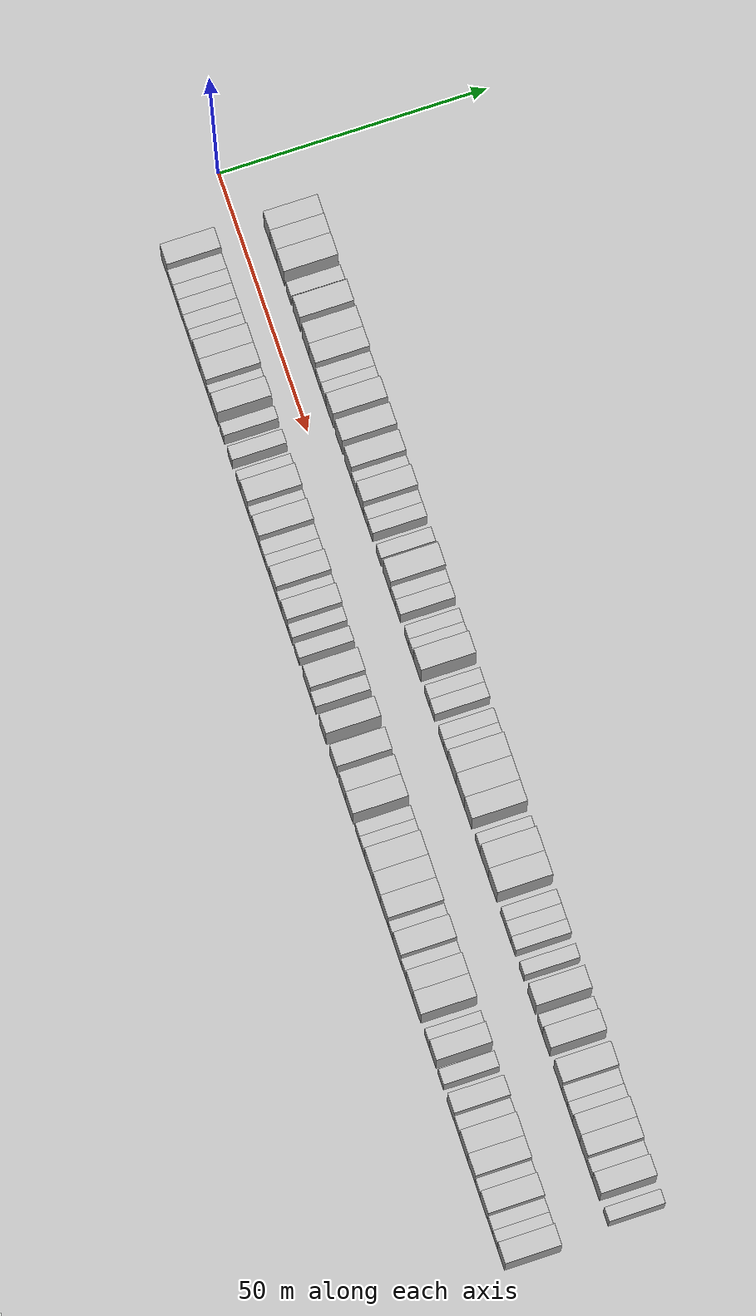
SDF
<?xml version="1.0" encoding="utf-8"?>

<sdf version="1.6">

   <world name="default">

      <gui fullscreen="0">

         <camera name="user_camera">

            <pose>-15 0 4.57585 0 0 0</pose>

            <view_controller>orbit</view_controller>

         </camera>

      </gui>

      <scene>

         <sky>

           <clouds>

             <speed>12</speed>

           </clouds>

         </sky>

         <ambient>0.4 0.4 0.4 1</ambient>

         <background>0.7 0.7 0.7 1</background>

         <shadows>1</shadows>

      </scene>

      <gravity>0 0 -9.8066</gravity>

      <magnetic_field>6e-06 2.3e-05 -4.2e-05</magnetic_field>

      <physics default="0" name="default_physics" type="ode">

         <ode>

            <solver>

               <type>quick</type>

               <iters>10</iters>

               <sor>1.0</sor>

               <use_dynamic_moi_rescaling>0</use_dynamic_moi_rescaling>

            </solver>

            <constraints>

               <cfm>0</cfm>

               <erp>0.2</erp>

               <contact_max_correcting_vel>100</contact_max_correcting_vel>

               <contact_surface_layer>0.001</contact_surface_layer>

            </constraints>

         </ode>

         <max_step_size>0.004</max_step_size>

         <real_time_factor>1</real_time_factor>

         <real_time_update_rate>250</real_time_update_rate>

      </physics>

      <light name="sun" type="directional">

         <cast_shadows>1</cast_shadows>

         <pose>0 0 10 0 0 0</pose>

         <diffuse>0.8 0.8 0.8 1</diffuse>

         <specular>0.2 0.2 0.2 1</specular>

         <attenuation>

            <range>1000</range>

            <constant>0.9</constant>

            <linear>0.01</linear>

            <quadratic>0.001</quadratic>

         </attenuation>

         <direction>-0.5 0.1 -0.9</direction>

      </light>

      <include>

         <name>ground_plane_1</name>

         <uri>model://HANNAS_ground_plane</uri>

         <pose>0 0 0  0 0 0</pose>

      </include>

      <include>

         <name>ground_plane_2</name>

         <uri>model://HANNAS_ground_plane</uri>

         <pose>100 0 0  0 0 0</pose>

      </include>

      <model name="building_1">

         <static>1</static>

         <pose frame="">13.8228 9.5000 0 0.000000 0.000000 1.570796</pose>

         <link name="link">

            <pose frame="">0 0 4.50 0 0 0</pose>

            <collision name="collision">

               <geometry>

                  <box>

                     <size>10.0000 3.6455 9.0000</size>

                  </box>

               </geometry>

               <max_contacts>10</max_contacts>

               <surface>

                  <contact>

                     <ode/>

                  </contact>

                  <bounce/>

                  <friction>

                     <torsional>

                        <ode/>

                     </torsional>

                     <ode/>

                  </friction>

               </surface>

            </collision>

            <visual name="visual">

               <cast_shadows>0</cast_shadows>

               <geometry>

                  <box>

                     <size>10.0000 3.6455 9.0000</size>

                  </box>

               </geometry>

               <material>

                  <script>

                     <uri>model://HANNAS_wall/materials/scripts</uri>

                     <uri>model://HANNAS_wall/materials/textures</uri>

                     <name>vrc/HANNAS_wall</name>

                  </script>

               </material>

            </visual>

            <self_collide>0</self_collide>

            <enable_wind>0</enable_wind>

            <kinematic>0</kinematic>

         </link>

      </model>

      <model name="building_2">

         <static>1</static>

         <pose frame="">17.5082 9.5000 0 0.000000 0.000000 1.570796</pose>

         <link name="link">

            <pose frame="">0 0 4.50 0 0 0</pose>

            <collision name="collision">

               <geometry>

                  <box>

                     <size>10.0000 3.7254 9.0000</size>

                  </box>

               </geometry>

               <max_contacts>10</max_contacts>

               <surface>

                  <contact>

                     <ode/>

                  </contact>

                  <bounce/>

                  <friction>

                     <torsional>

                        <ode/>

                     </torsional>

                     <ode/>

                  </friction>

               </surface>

            </collision>

            <visual name="visual">

               <cast_shadows>0</cast_shadows>

               <geometry>

                  <box>

                     <size>10.0000 3.7254 9.0000</size>

                  </box>

               </geometry>

               <material>

                  <script>

                     <uri>model://HANNAS_wall/materials/scripts</uri>

                     <uri>model://HANNAS_wall/materials/textures</uri>

                     <name>vrc/HANNAS_wall</name>

                  </script>

               </material>

            </visual>

            <self_collide>0</self_collide>

            <enable_wind>0</enable_wind>

            <kinematic>0</kinematic>

         </link>

      </model>

      <model name="building_3">

         <static>1</static>

         <pose frame="">21.4982 9.5000 0 0.000000 0.000000 1.570796</pose>

         <link name="link">

            <pose frame="">0 0 4.50 0 0 0</pose>

            <collision name="collision">

               <geometry>

                  <box>

                     <size>10.0000 4.2545 9.0000</size>

                  </box>

               </geometry>

               <max_contacts>10</max_contacts>

               <surface>

                  <contact>

                     <ode/>

                  </contact>

                  <bounce/>

                  <friction>

                     <torsional>

                        <ode/>

                     </torsional>

                     <ode/>

                  </friction>

               </surface>

            </collision>

            <visual name="visual">

               <cast_shadows>0</cast_shadows>

               <geometry>

                  <box>

                     <size>10.0000 4.2545 9.0000</size>

                  </box>

               </geometry>

               <material>

                  <script>

                     <uri>model://HANNAS_wall/materials/scripts</uri>

                     <uri>model://HANNAS_wall/materials/textures</uri>

                     <name>vrc/HANNAS_wall</name>

                  </script>

               </material>

            </visual>

            <self_collide>0</self_collide>

            <enable_wind>0</enable_wind>

            <kinematic>0</kinematic>

         </link>

      </model>

      <model name="building_4">

         <static>1</static>

         <pose frame="">26.0055 9.5000 0 0.000000 0.000000 1.570796</pose>

         <link name="link">

            <pose frame="">0 0 3.00 0 0 0</pose>

            <collision name="collision">

               <geometry>

                  <box>

                     <size>10.0000 2.7602 6.0000</size>

                  </box>

               </geometry>

               <max_contacts>10</max_contacts>

               <surface>

                  <contact>

                     <ode/>

                  </contact>

                  <bounce/>

                  <friction>

                     <torsional>

                        <ode/>

                     </torsional>

                     <ode/>

                  </friction>

               </surface>

            </collision>

            <visual name="visual">

               <cast_shadows>0</cast_shadows>

               <geometry>

                  <box>

                     <size>10.0000 2.7602 6.0000</size>

                  </box>

               </geometry>

               <material>

                  <script>

                     <uri>model://HANNAS_wall/materials/scripts</uri>

                     <uri>model://HANNAS_wall/materials/textures</uri>

                     <name>vrc/HANNAS_wall</name>

                  </script>

               </material>

            </visual>

            <self_collide>0</self_collide>

            <enable_wind>0</enable_wind>

            <kinematic>0</kinematic>

         </link>

      </model>

      <model name="building_5">

         <static>1</static>

         <pose frame="">30.4323 9.5000 0 0.000000 0.000000 1.570796</pose>

         <link name="link">

            <pose frame="">0 0 4.50 0 0 0</pose>

            <collision name="collision">

               <geometry>

                  <box>

                     <size>10.0000 4.0935 9.0000</size>

                  </box>

               </geometry>

               <max_contacts>10</max_contacts>

               <surface>

                  <contact>

                     <ode/>

                  </contact>

                  <bounce/>

                  <friction>

                     <torsional>

                        <ode/>

                     </torsional>

                     <ode/>

                  </friction>

               </surface>

            </collision>

            <visual name="visual">

               <cast_shadows>0</cast_shadows>

               <geometry>

                  <box>

                     <size>10.0000 4.0935 9.0000</size>

                  </box>

               </geometry>

               <material>

                  <script>

                     <uri>model://HANNAS_wall/materials/scripts</uri>

                     <uri>model://HANNAS_wall/materials/textures</uri>

                     <name>vrc/HANNAS_wall</name>

                  </script>

               </material>

            </visual>

            <self_collide>0</self_collide>

            <enable_wind>0</enable_wind>

            <kinematic>0</kinematic>

         </link>

      </model>

      <model name="building_6">

         <static>1</static>

         <pose frame="">35.4440 9.5000 0 0.000000 0.000000 1.570796</pose>

         <link name="link">

            <pose frame="">0 0 4.50 0 0 0</pose>

            <collision name="collision">

               <geometry>

                  <box>

                     <size>10.0000 3.9298 9.0000</size>

                  </box>

               </geometry>

               <max_contacts>10</max_contacts>

               <surface>

                  <contact>

                     <ode/>

                  </contact>

                  <bounce/>

                  <friction>

                     <torsional>

                        <ode/>

                     </torsional>

                     <ode/>

                  </friction>

               </surface>

            </collision>

            <visual name="visual">

               <cast_shadows>0</cast_shadows>

               <geometry>

                  <box>

                     <size>10.0000 3.9298 9.0000</size>

                  </box>

               </geometry>

               <material>

                  <script>

                     <uri>model://HANNAS_wall/materials/scripts</uri>

                     <uri>model://HANNAS_wall/materials/textures</uri>

                     <name>vrc/HANNAS_wall</name>

                  </script>

               </material>

            </visual>

            <self_collide>0</self_collide>

            <enable_wind>0</enable_wind>

            <kinematic>0</kinematic>

         </link>

      </model>

      <model name="building_7">

         <static>1</static>

         <pose frame="">39.3031 9.5000 0 0.000000 0.000000 1.570796</pose>

         <link name="link">

            <pose frame="">0 0 4.50 0 0 0</pose>

            <collision name="collision">

               <geometry>

                  <box>

                     <size>10.0000 3.7886 9.0000</size>

                  </box>

               </geometry>

               <max_contacts>10</max_contacts>

               <surface>

                  <contact>

                     <ode/>

                  </contact>

                  <bounce/>

                  <friction>

                     <torsional>

                        <ode/>

                     </torsional>

                     <ode/>

                  </friction>

               </surface>

            </collision>

            <visual name="visual">

               <cast_shadows>0</cast_shadows>

               <geometry>

                  <box>

                     <size>10.0000 3.7886 9.0000</size>

                  </box>

               </geometry>

               <material>

                  <script>

                     <uri>model://HANNAS_wall/materials/scripts</uri>

                     <uri>model://HANNAS_wall/materials/textures</uri>

                     <name>vrc/HANNAS_wall</name>

                  </script>

               </material>

            </visual>

            <self_collide>0</self_collide>

            <enable_wind>0</enable_wind>

            <kinematic>0</kinematic>

         </link>

      </model>

      <model name="building_8">

         <static>1</static>

         <pose frame="">42.5841 9.5000 0 0.000000 0.000000 1.570796</pose>

         <link name="link">

            <pose frame="">0 0 3.00 0 0 0</pose>

            <collision name="collision">

               <geometry>

                  <box>

                     <size>10.0000 2.7733 6.0000</size>

                  </box>

               </geometry>

               <max_contacts>10</max_contacts>

               <surface>

                  <contact>

                     <ode/>

                  </contact>

                  <bounce/>

                  <friction>

                     <torsional>

                        <ode/>

                     </torsional>

                     <ode/>

                  </friction>

               </surface>

            </collision>

            <visual name="visual">

               <cast_shadows>0</cast_shadows>

               <geometry>

                  <box>

                     <size>10.0000 2.7733 6.0000</size>

                  </box>

               </geometry>

               <material>

                  <script>

                     <uri>model://HANNAS_wall/materials/scripts</uri>

                     <uri>model://HANNAS_wall/materials/textures</uri>

                     <name>vrc/HANNAS_wall</name>

                  </script>

               </material>

            </visual>

            <self_collide>0</self_collide>

            <enable_wind>0</enable_wind>

            <kinematic>0</kinematic>

         </link>

      </model>

      <model name="building_9">

         <static>1</static>

         <pose frame="">45.4373 9.5000 0 0.000000 0.000000 1.570796</pose>

         <link name="link">

            <pose frame="">0 0 3.00 0 0 0</pose>

            <collision name="collision">

               <geometry>

                  <box>

                     <size>10.0000 2.9332 6.0000</size>

                  </box>

               </geometry>

               <max_contacts>10</max_contacts>

               <surface>

                  <contact>

                     <ode/>

                  </contact>

                  <bounce/>

                  <friction>

                     <torsional>

                        <ode/>

                     </torsional>

                     <ode/>

                  </friction>

               </surface>

            </collision>

            <visual name="visual">

               <cast_shadows>0</cast_shadows>

               <geometry>

                  <box>

                     <size>10.0000 2.9332 6.0000</size>

                  </box>

               </geometry>

               <material>

                  <script>

                     <uri>model://HANNAS_wall/materials/scripts</uri>

                     <uri>model://HANNAS_wall/materials/textures</uri>

                     <name>vrc/HANNAS_wall</name>

                  </script>

               </material>

            </visual>

            <self_collide>0</self_collide>

            <enable_wind>0</enable_wind>

            <kinematic>0</kinematic>

         </link>

      </model>

      <model name="building_10">

         <static>1</static>

         <pose frame="">48.9115 9.5000 0 0.000000 0.000000 1.570796</pose>

         <link name="link">

            <pose frame="">0 0 4.50 0 0 0</pose>

            <collision name="collision">

               <geometry>

                  <box>

                     <size>10.0000 4.0150 9.0000</size>

                  </box>

               </geometry>

               <max_contacts>10</max_contacts>

               <surface>

                  <contact>

                     <ode/>

                  </contact>

                  <bounce/>

                  <friction>

                     <torsional>

                        <ode/>

                     </torsional>

                     <ode/>

                  </friction>

               </surface>

            </collision>

            <visual name="visual">

               <cast_shadows>0</cast_shadows>

               <geometry>

                  <box>

                     <size>10.0000 4.0150 9.0000</size>

                  </box>

               </geometry>

               <material>

                  <script>

                     <uri>model://HANNAS_wall/materials/scripts</uri>

                     <uri>model://HANNAS_wall/materials/textures</uri>

                     <name>vrc/HANNAS_wall</name>

                  </script>

               </material>

            </visual>

            <self_collide>0</self_collide>

            <enable_wind>0</enable_wind>

            <kinematic>0</kinematic>

         </link>

      </model>

      <model name="building_11">

         <static>1</static>

         <pose frame="">53.9710 9.5000 0 0.000000 0.000000 1.570796</pose>

         <link name="link">

            <pose frame="">0 0 4.50 0 0 0</pose>

            <collision name="collision">

               <geometry>

                  <box>

                     <size>10.0000 4.1041 9.0000</size>

                  </box>

               </geometry>

               <max_contacts>10</max_contacts>

               <surface>

                  <contact>

                     <ode/>

                  </contact>

                  <bounce/>

                  <friction>

                     <torsional>

                        <ode/>

                     </torsional>

                     <ode/>

                  </friction>

               </surface>

            </collision>

            <visual name="visual">

               <cast_shadows>0</cast_shadows>

               <geometry>

                  <box>

                     <size>10.0000 4.1041 9.0000</size>

                  </box>

               </geometry>

               <material>

                  <script>

                     <uri>model://HANNAS_wall/materials/scripts</uri>

                     <uri>model://HANNAS_wall/materials/textures</uri>

                     <name>vrc/HANNAS_wall</name>

                  </script>

               </material>

            </visual>

            <self_collide>0</self_collide>

            <enable_wind>0</enable_wind>

            <kinematic>0</kinematic>

         </link>

      </model>

      <model name="building_12">

         <static>1</static>

         <pose frame="">59.0237 9.5000 0 0.000000 0.000000 1.570796</pose>

         <link name="link">

            <pose frame="">0 0 4.50 0 0 0</pose>

            <collision name="collision">

               <geometry>

                  <box>

                     <size>10.0000 4.0014 9.0000</size>

                  </box>

               </geometry>

               <max_contacts>10</max_contacts>

               <surface>

                  <contact>

                     <ode/>

                  </contact>

                  <bounce/>

                  <friction>

                     <torsional>

                        <ode/>

                     </torsional>

                     <ode/>

                  </friction>

               </surface>

            </collision>

            <visual name="visual">

               <cast_shadows>0</cast_shadows>

               <geometry>

                  <box>

                     <size>10.0000 4.0014 9.0000</size>

                  </box>

               </geometry>

               <material>

                  <script>

                     <uri>model://HANNAS_wall/materials/scripts</uri>

                     <uri>model://HANNAS_wall/materials/textures</uri>

                     <name>vrc/HANNAS_wall</name>

                  </script>

               </material>

            </visual>

            <self_collide>0</self_collide>

            <enable_wind>0</enable_wind>

            <kinematic>0</kinematic>

         </link>

      </model>

      <model name="building_13">

         <static>1</static>

         <pose frame="">62.3560 9.5000 0 0.000000 0.000000 1.570796</pose>

         <link name="link">

            <pose frame="">0 0 3.00 0 0 0</pose>

            <collision name="collision">

               <geometry>

                  <box>

                     <size>10.0000 2.6633 6.0000</size>

                  </box>

               </geometry>

               <max_contacts>10</max_contacts>

               <surface>

                  <contact>

                     <ode/>

                  </contact>

                  <bounce/>

                  <friction>

                     <torsional>

                        <ode/>

                     </torsional>

                     <ode/>

                  </friction>

               </surface>

            </collision>

            <visual name="visual">

               <cast_shadows>0</cast_shadows>

               <geometry>

                  <box>

                     <size>10.0000 2.6633 6.0000</size>

                  </box>

               </geometry>

               <material>

                  <script>

                     <uri>model://HANNAS_wall/materials/scripts</uri>

                     <uri>model://HANNAS_wall/materials/textures</uri>

                     <name>vrc/HANNAS_wall</name>

                  </script>

               </material>

            </visual>

            <self_collide>0</self_collide>

            <enable_wind>0</enable_wind>

            <kinematic>0</kinematic>

         </link>

      </model>

      <model name="building_14">

         <static>1</static>

         <pose frame="">65.6383 9.5000 0 0.000000 0.000000 1.570796</pose>

         <link name="link">

            <pose frame="">0 0 4.50 0 0 0</pose>

            <collision name="collision">

               <geometry>

                  <box>

                     <size>10.0000 3.9012 9.0000</size>

                  </box>

               </geometry>

               <max_contacts>10</max_contacts>

               <surface>

                  <contact>

                     <ode/>

                  </contact>

                  <bounce/>

                  <friction>

                     <torsional>

                        <ode/>

                     </torsional>

                     <ode/>

                  </friction>

               </surface>

            </collision>

            <visual name="visual">

               <cast_shadows>0</cast_shadows>

               <geometry>

                  <box>

                     <size>10.0000 3.9012 9.0000</size>

                  </box>

               </geometry>

               <material>

                  <script>

                     <uri>model://HANNAS_wall/materials/scripts</uri>

                     <uri>model://HANNAS_wall/materials/textures</uri>

                     <name>vrc/HANNAS_wall</name>

                  </script>

               </material>

            </visual>

            <self_collide>0</self_collide>

            <enable_wind>0</enable_wind>

            <kinematic>0</kinematic>

         </link>

      </model>

      <model name="building_15">

         <static>1</static>

         <pose frame="">68.8008 9.5000 0 0.000000 0.000000 1.570796</pose>

         <link name="link">

            <pose frame="">0 0 3.00 0 0 0</pose>

            <collision name="collision">

               <geometry>

                  <box>

                     <size>10.0000 2.4239 6.0000</size>

                  </box>

               </geometry>

               <max_contacts>10</max_contacts>

               <surface>

                  <contact>

                     <ode/>

                  </contact>

                  <bounce/>

                  <friction>

                     <torsional>

                        <ode/>

                     </torsional>

                     <ode/>

                  </friction>

               </surface>

            </collision>

            <visual name="visual">

               <cast_shadows>0</cast_shadows>

               <geometry>

                  <box>

                     <size>10.0000 2.4239 6.0000</size>

                  </box>

               </geometry>

               <material>

                  <script>

                     <uri>model://HANNAS_wall/materials/scripts</uri>

                     <uri>model://HANNAS_wall/materials/textures</uri>

                     <name>vrc/HANNAS_wall</name>

                  </script>

               </material>

            </visual>

            <self_collide>0</self_collide>

            <enable_wind>0</enable_wind>

            <kinematic>0</kinematic>

         </link>

      </model>

      <model name="building_16">

         <static>1</static>

         <pose frame="">71.3409 9.5000 0 0.000000 0.000000 1.570796</pose>

         <link name="link">

            <pose frame="">0 0 3.00 0 0 0</pose>

            <collision name="collision">

               <geometry>

                  <box>

                     <size>10.0000 2.6561 6.0000</size>

                  </box>

               </geometry>

               <max_contacts>10</max_contacts>

               <surface>

                  <contact>

                     <ode/>

                  </contact>

                  <bounce/>

                  <friction>

                     <torsional>

                        <ode/>

                     </torsional>

                     <ode/>

                  </friction>

               </surface>

            </collision>

            <visual name="visual">

               <cast_shadows>0</cast_shadows>

               <geometry>

                  <box>

                     <size>10.0000 2.6561 6.0000</size>

                  </box>

               </geometry>

               <material>

                  <script>

                     <uri>model://HANNAS_wall/materials/scripts</uri>

                     <uri>model://HANNAS_wall/materials/textures</uri>

                     <name>vrc/HANNAS_wall</name>

                  </script>

               </material>

            </visual>

            <self_collide>0</self_collide>

            <enable_wind>0</enable_wind>

            <kinematic>0</kinematic>

         </link>

      </model>

      <model name="building_17">

         <static>1</static>

         <pose frame="">76.0085 9.5000 0 0.000000 0.000000 1.570796</pose>

         <link name="link">

            <pose frame="">0 0 3.00 0 0 0</pose>

            <collision name="collision">

               <geometry>

                  <box>

                     <size>10.0000 2.6791 6.0000</size>

                  </box>

               </geometry>

               <max_contacts>10</max_contacts>

               <surface>

                  <contact>

                     <ode/>

                  </contact>

                  <bounce/>

                  <friction>

                     <torsional>

                        <ode/>

                     </torsional>

                     <ode/>

                  </friction>

               </surface>

            </collision>

            <visual name="visual">

               <cast_shadows>0</cast_shadows>

               <geometry>

                  <box>

                     <size>10.0000 2.6791 6.0000</size>

                  </box>

               </geometry>

               <material>

                  <script>

                     <uri>model://HANNAS_wall/materials/scripts</uri>

                     <uri>model://HANNAS_wall/materials/textures</uri>

                     <name>vrc/HANNAS_wall</name>

                  </script>

               </material>

            </visual>

            <self_collide>0</self_collide>

            <enable_wind>0</enable_wind>

            <kinematic>0</kinematic>

         </link>

      </model>

      <model name="building_18">

         <static>1</static>

         <pose frame="">80.4945 9.5000 0 0.000000 0.000000 1.570796</pose>

         <link name="link">

            <pose frame="">0 0 4.50 0 0 0</pose>

            <collision name="collision">

               <geometry>

                  <box>

                     <size>10.0000 4.2929 9.0000</size>

                  </box>

               </geometry>

               <max_contacts>10</max_contacts>

               <surface>

                  <contact>

                     <ode/>

                  </contact>

                  <bounce/>

                  <friction>

                     <torsional>

                        <ode/>

                     </torsional>

                     <ode/>

                  </friction>

               </surface>

            </collision>

            <visual name="visual">

               <cast_shadows>0</cast_shadows>

               <geometry>

                  <box>

                     <size>10.0000 4.2929 9.0000</size>

                  </box>

               </geometry>

               <material>

                  <script>

                     <uri>model://HANNAS_wall/materials/scripts</uri>

                     <uri>model://HANNAS_wall/materials/textures</uri>

                     <name>vrc/HANNAS_wall</name>

                  </script>

               </material>

            </visual>

            <self_collide>0</self_collide>

            <enable_wind>0</enable_wind>

            <kinematic>0</kinematic>

         </link>

      </model>

      <model name="building_19">

         <static>1</static>

         <pose frame="">83.8605 9.5000 0 0.000000 0.000000 1.570796</pose>

         <link name="link">

            <pose frame="">0 0 3.00 0 0 0</pose>

            <collision name="collision">

               <geometry>

                  <box>

                     <size>10.0000 2.4390 6.0000</size>

                  </box>

               </geometry>

               <max_contacts>10</max_contacts>

               <surface>

                  <contact>

                     <ode/>

                  </contact>

                  <bounce/>

                  <friction>

                     <torsional>

                        <ode/>

                     </torsional>

                     <ode/>

                  </friction>

               </surface>

            </collision>

            <visual name="visual">

               <cast_shadows>0</cast_shadows>

               <geometry>

                  <box>

                     <size>10.0000 2.4390 6.0000</size>

                  </box>

               </geometry>

               <material>

                  <script>

                     <uri>model://HANNAS_wall/materials/scripts</uri>

                     <uri>model://HANNAS_wall/materials/textures</uri>

                     <name>vrc/HANNAS_wall</name>

                  </script>

               </material>

            </visual>

            <self_collide>0</self_collide>

            <enable_wind>0</enable_wind>

            <kinematic>0</kinematic>

         </link>

      </model>

      <model name="building_20">

         <static>1</static>

         <pose frame="">86.5218 9.5000 0 0.000000 0.000000 1.570796</pose>

         <link name="link">

            <pose frame="">0 0 3.00 0 0 0</pose>

            <collision name="collision">

               <geometry>

                  <box>

                     <size>10.0000 2.8836 6.0000</size>

                  </box>

               </geometry>

               <max_contacts>10</max_contacts>

               <surface>

                  <contact>

                     <ode/>

                  </contact>

                  <bounce/>

                  <friction>

                     <torsional>

                        <ode/>

                     </torsional>

                     <ode/>

                  </friction>

               </surface>

            </collision>

            <visual name="visual">

               <cast_shadows>0</cast_shadows>

               <geometry>

                  <box>

                     <size>10.0000 2.8836 6.0000</size>

                  </box>

               </geometry>

               <material>

                  <script>

                     <uri>model://HANNAS_wall/materials/scripts</uri>

                     <uri>model://HANNAS_wall/materials/textures</uri>

                     <name>vrc/HANNAS_wall</name>

                  </script>

               </material>

            </visual>

            <self_collide>0</self_collide>

            <enable_wind>0</enable_wind>

            <kinematic>0</kinematic>

         </link>

      </model>

      <model name="building_21">

         <static>1</static>

         <pose frame="">91.2309 9.5000 0 0.000000 0.000000 1.570796</pose>

         <link name="link">

            <pose frame="">0 0 3.00 0 0 0</pose>

            <collision name="collision">

               <geometry>

                  <box>

                     <size>10.0000 2.5348 6.0000</size>

                  </box>

               </geometry>

               <max_contacts>10</max_contacts>

               <surface>

                  <contact>

                     <ode/>

                  </contact>

                  <bounce/>

                  <friction>

                     <torsional>

                        <ode/>

                     </torsional>

                     <ode/>

                  </friction>

               </surface>

            </collision>

            <visual name="visual">

               <cast_shadows>0</cast_shadows>

               <geometry>

                  <box>

                     <size>10.0000 2.5348 6.0000</size>

                  </box>

               </geometry>

               <material>

                  <script>

                     <uri>model://HANNAS_wall/materials/scripts</uri>

                     <uri>model://HANNAS_wall/materials/textures</uri>

                     <name>vrc/HANNAS_wall</name>

                  </script>

               </material>

            </visual>

            <self_collide>0</self_collide>

            <enable_wind>0</enable_wind>

            <kinematic>0</kinematic>

         </link>

      </model>

      <model name="building_22">

         <static>1</static>

         <pose frame="">93.7545 9.5000 0 0.000000 0.000000 1.570796</pose>

         <link name="link">

            <pose frame="">0 0 3.00 0 0 0</pose>

            <collision name="collision">

               <geometry>

                  <box>

                     <size>10.0000 2.5124 6.0000</size>

                  </box>

               </geometry>

               <max_contacts>10</max_contacts>

               <surface>

                  <contact>

                     <ode/>

                  </contact>

                  <bounce/>

                  <friction>

                     <torsional>

                        <ode/>

                     </torsional>

                     <ode/>

                  </friction>

               </surface>

            </collision>

            <visual name="visual">

               <cast_shadows>0</cast_shadows>

               <geometry>

                  <box>

                     <size>10.0000 2.5124 6.0000</size>

                  </box>

               </geometry>

               <material>

                  <script>

                     <uri>model://HANNAS_wall/materials/scripts</uri>

                     <uri>model://HANNAS_wall/materials/textures</uri>

                     <name>vrc/HANNAS_wall</name>

                  </script>

               </material>

            </visual>

            <self_collide>0</self_collide>

            <enable_wind>0</enable_wind>

            <kinematic>0</kinematic>

         </link>

      </model>

      <model name="building_23">

         <static>1</static>

         <pose frame="">97.0483 9.5000 0 0.000000 0.000000 1.570796</pose>

         <link name="link">

            <pose frame="">0 0 4.50 0 0 0</pose>

            <collision name="collision">

               <geometry>

                  <box>

                     <size>10.0000 4.0752 9.0000</size>

                  </box>

               </geometry>

               <max_contacts>10</max_contacts>

               <surface>

                  <contact>

                     <ode/>

                  </contact>

                  <bounce/>

                  <friction>

                     <torsional>

                        <ode/>

                     </torsional>

                     <ode/>

                  </friction>

               </surface>

            </collision>

            <visual name="visual">

               <cast_shadows>0</cast_shadows>

               <geometry>

                  <box>

                     <size>10.0000 4.0752 9.0000</size>

                  </box>

               </geometry>

               <material>

                  <script>

                     <uri>model://HANNAS_wall/materials/scripts</uri>

                     <uri>model://HANNAS_wall/materials/textures</uri>

                     <name>vrc/HANNAS_wall</name>

                  </script>

               </material>

            </visual>

            <self_collide>0</self_collide>

            <enable_wind>0</enable_wind>

            <kinematic>0</kinematic>

         </link>

      </model>

      <model name="building_24">

         <static>1</static>

         <pose frame="">102.4143 9.5000 0 0.000000 0.000000 1.570796</pose>

         <link name="link">

            <pose frame="">0 0 3.00 0 0 0</pose>

            <collision name="collision">

               <geometry>

                  <box>

                     <size>10.0000 2.6569 6.0000</size>

                  </box>

               </geometry>

               <max_contacts>10</max_contacts>

               <surface>

                  <contact>

                     <ode/>

                  </contact>

                  <bounce/>

                  <friction>

                     <torsional>

                        <ode/>

                     </torsional>

                     <ode/>

                  </friction>

               </surface>

            </collision>

            <visual name="visual">

               <cast_shadows>0</cast_shadows>

               <geometry>

                  <box>

                     <size>10.0000 2.6569 6.0000</size>

                  </box>

               </geometry>

               <material>

                  <script>

                     <uri>model://HANNAS_wall/materials/scripts</uri>

                     <uri>model://HANNAS_wall/materials/textures</uri>

                     <name>vrc/HANNAS_wall</name>

                  </script>

               </material>

            </visual>

            <self_collide>0</self_collide>

            <enable_wind>0</enable_wind>

            <kinematic>0</kinematic>

         </link>

      </model>

      <model name="building_25">

         <static>1</static>

         <pose frame="">105.1513 9.5000 0 0.000000 0.000000 1.570796</pose>

         <link name="link">

            <pose frame="">0 0 3.00 0 0 0</pose>

            <collision name="collision">

               <geometry>

                  <box>

                     <size>10.0000 2.8169 6.0000</size>

                  </box>

               </geometry>

               <max_contacts>10</max_contacts>

               <surface>

                  <contact>

                     <ode/>

                  </contact>

                  <bounce/>

                  <friction>

                     <torsional>

                        <ode/>

                     </torsional>

                     <ode/>

                  </friction>

               </surface>

            </collision>

            <visual name="visual">

               <cast_shadows>0</cast_shadows>

               <geometry>

                  <box>

                     <size>10.0000 2.8169 6.0000</size>

                  </box>

               </geometry>

               <material>

                  <script>

                     <uri>model://HANNAS_wall/materials/scripts</uri>

                     <uri>model://HANNAS_wall/materials/textures</uri>

                     <name>vrc/HANNAS_wall</name>

                  </script>

               </material>

            </visual>

            <self_collide>0</self_collide>

            <enable_wind>0</enable_wind>

            <kinematic>0</kinematic>

         </link>

      </model>

      <model name="building_26">

         <static>1</static>

         <pose frame="">109.9169 9.5000 0 0.000000 0.000000 1.570796</pose>

         <link name="link">

            <pose frame="">0 0 3.00 0 0 0</pose>

            <collision name="collision">

               <geometry>

                  <box>

                     <size>10.0000 2.7142 6.0000</size>

                  </box>

               </geometry>

               <max_contacts>10</max_contacts>

               <surface>

                  <contact>

                     <ode/>

                  </contact>

                  <bounce/>

                  <friction>

                     <torsional>

                        <ode/>

                     </torsional>

                     <ode/>

                  </friction>

               </surface>

            </collision>

            <visual name="visual">

               <cast_shadows>0</cast_shadows>

               <geometry>

                  <box>

                     <size>10.0000 2.7142 6.0000</size>

                  </box>

               </geometry>

               <material>

                  <script>

                     <uri>model://HANNAS_wall/materials/scripts</uri>

                     <uri>model://HANNAS_wall/materials/textures</uri>

                     <name>vrc/HANNAS_wall</name>

                  </script>

               </material>

            </visual>

            <self_collide>0</self_collide>

            <enable_wind>0</enable_wind>

            <kinematic>0</kinematic>

         </link>

      </model>

      <model name="building_27">

         <static>1</static>

         <pose frame="">112.5251 9.5000 0 0.000000 0.000000 1.570796</pose>

         <link name="link">

            <pose frame="">0 0 3.00 0 0 0</pose>

            <collision name="collision">

               <geometry>

                  <box>

                     <size>10.0000 2.5022 6.0000</size>

                  </box>

               </geometry>

               <max_contacts>10</max_contacts>

               <surface>

                  <contact>

                     <ode/>

                  </contact>

                  <bounce/>

                  <friction>

                     <torsional>

                        <ode/>

                     </torsional>

                     <ode/>

                  </friction>

               </surface>

            </collision>

            <visual name="visual">

               <cast_shadows>0</cast_shadows>

               <geometry>

                  <box>

                     <size>10.0000 2.5022 6.0000</size>

                  </box>

               </geometry>

               <material>

                  <script>

                     <uri>model://HANNAS_wall/materials/scripts</uri>

                     <uri>model://HANNAS_wall/materials/textures</uri>

                     <name>vrc/HANNAS_wall</name>

                  </script>

               </material>

            </visual>

            <self_collide>0</self_collide>

            <enable_wind>0</enable_wind>

            <kinematic>0</kinematic>

         </link>

      </model>

      <model name="building_28">

         <static>1</static>

         <pose frame="">115.9399 9.5000 0 0.000000 0.000000 1.570796</pose>

         <link name="link">

            <pose frame="">0 0 4.50 0 0 0</pose>

            <collision name="collision">

               <geometry>

                  <box>

                     <size>10.0000 4.3274 9.0000</size>

                  </box>

               </geometry>

               <max_contacts>10</max_contacts>

               <surface>

                  <contact>

                     <ode/>

                  </contact>

                  <bounce/>

                  <friction>

                     <torsional>

                        <ode/>

                     </torsional>

                     <ode/>

                  </friction>

               </surface>

            </collision>

            <visual name="visual">

               <cast_shadows>0</cast_shadows>

               <geometry>

                  <box>

                     <size>10.0000 4.3274 9.0000</size>

                  </box>

               </geometry>

               <material>

                  <script>

                     <uri>model://HANNAS_wall/materials/scripts</uri>

                     <uri>model://HANNAS_wall/materials/textures</uri>

                     <name>vrc/HANNAS_wall</name>

                  </script>

               </material>

            </visual>

            <self_collide>0</self_collide>

            <enable_wind>0</enable_wind>

            <kinematic>0</kinematic>

         </link>

      </model>

      <model name="building_29">

         <static>1</static>

         <pose frame="">120.3343 9.5000 0 0.000000 0.000000 1.570796</pose>

         <link name="link">

            <pose frame="">0 0 4.50 0 0 0</pose>

            <collision name="collision">

               <geometry>

                  <box>

                     <size>10.0000 4.4612 9.0000</size>

                  </box>

               </geometry>

               <max_contacts>10</max_contacts>

               <surface>

                  <contact>

                     <ode/>

                  </contact>

                  <bounce/>

                  <friction>

                     <torsional>

                        <ode/>

                     </torsional>

                     <ode/>

                  </friction>

               </surface>

            </collision>

            <visual name="visual">

               <cast_shadows>0</cast_shadows>

               <geometry>

                  <box>

                     <size>10.0000 4.4612 9.0000</size>

                  </box>

               </geometry>

               <material>

                  <script>

                     <uri>model://HANNAS_wall/materials/scripts</uri>

                     <uri>model://HANNAS_wall/materials/textures</uri>

                     <name>vrc/HANNAS_wall</name>

                  </script>

               </material>

            </visual>

            <self_collide>0</self_collide>

            <enable_wind>0</enable_wind>

            <kinematic>0</kinematic>

         </link>

      </model>

      <model name="building_30">

         <static>1</static>

         <pose frame="">124.5504 9.5000 0 0.000000 0.000000 1.570796</pose>

         <link name="link">

            <pose frame="">0 0 4.50 0 0 0</pose>

            <collision name="collision">

               <geometry>

                  <box>

                     <size>10.0000 3.9710 9.0000</size>

                  </box>

               </geometry>

               <max_contacts>10</max_contacts>

               <surface>

                  <contact>

                     <ode/>

                  </contact>

                  <bounce/>

                  <friction>

                     <torsional>

                        <ode/>

                     </torsional>

                     <ode/>

                  </friction>

               </surface>

            </collision>

            <visual name="visual">

               <cast_shadows>0</cast_shadows>

               <geometry>

                  <box>

                     <size>10.0000 3.9710 9.0000</size>

                  </box>

               </geometry>

               <material>

                  <script>

                     <uri>model://HANNAS_wall/materials/scripts</uri>

                     <uri>model://HANNAS_wall/materials/textures</uri>

                     <name>vrc/HANNAS_wall</name>

                  </script>

               </material>

            </visual>

            <self_collide>0</self_collide>

            <enable_wind>0</enable_wind>

            <kinematic>0</kinematic>

         </link>

      </model>

      <model name="building_31">

         <static>1</static>

         <pose frame="">129.8526 9.5000 0 0.000000 0.000000 1.570796</pose>

         <link name="link">

            <pose frame="">0 0 3.00 0 0 0</pose>

            <collision name="collision">

               <geometry>

                  <box>

                     <size>10.0000 2.6334 6.0000</size>

                  </box>

               </geometry>

               <max_contacts>10</max_contacts>

               <surface>

                  <contact>

                     <ode/>

                  </contact>

                  <bounce/>

                  <friction>

                     <torsional>

                        <ode/>

                     </torsional>

                     <ode/>

                  </friction>

               </surface>

            </collision>

            <visual name="visual">

               <cast_shadows>0</cast_shadows>

               <geometry>

                  <box>

                     <size>10.0000 2.6334 6.0000</size>

                  </box>

               </geometry>

               <material>

                  <script>

                     <uri>model://HANNAS_wall/materials/scripts</uri>

                     <uri>model://HANNAS_wall/materials/textures</uri>

                     <name>vrc/HANNAS_wall</name>

                  </script>

               </material>

            </visual>

            <self_collide>0</self_collide>

            <enable_wind>0</enable_wind>

            <kinematic>0</kinematic>

         </link>

      </model>

      <model name="building_32">

         <static>1</static>

         <pose frame="">133.3780 9.5000 0 0.000000 0.000000 1.570796</pose>

         <link name="link">

            <pose frame="">0 0 4.50 0 0 0</pose>

            <collision name="collision">

               <geometry>

                  <box>

                     <size>10.0000 4.4174 9.0000</size>

                  </box>

               </geometry>

               <max_contacts>10</max_contacts>

               <surface>

                  <contact>

                     <ode/>

                  </contact>

                  <bounce/>

                  <friction>

                     <torsional>

                        <ode/>

                     </torsional>

                     <ode/>

                  </friction>

               </surface>

            </collision>

            <visual name="visual">

               <cast_shadows>0</cast_shadows>

               <geometry>

                  <box>

                     <size>10.0000 4.4174 9.0000</size>

                  </box>

               </geometry>

               <material>

                  <script>

                     <uri>model://HANNAS_wall/materials/scripts</uri>

                     <uri>model://HANNAS_wall/materials/textures</uri>

                     <name>vrc/HANNAS_wall</name>

                  </script>

               </material>

            </visual>

            <self_collide>0</self_collide>

            <enable_wind>0</enable_wind>

            <kinematic>0</kinematic>

         </link>

      </model>

      <model name="building_33">

         <static>1</static>

         <pose frame="">137.8079 9.5000 0 0.000000 0.000000 1.570796</pose>

         <link name="link">

            <pose frame="">0 0 4.50 0 0 0</pose>

            <collision name="collision">

               <geometry>

                  <box>

                     <size>10.0000 4.4425 9.0000</size>

                  </box>

               </geometry>

               <max_contacts>10</max_contacts>

               <surface>

                  <contact>

                     <ode/>

                  </contact>

                  <bounce/>

                  <friction>

                     <torsional>

                        <ode/>

                     </torsional>

                     <ode/>

                  </friction>

               </surface>

            </collision>

            <visual name="visual">

               <cast_shadows>0</cast_shadows>

               <geometry>

                  <box>

                     <size>10.0000 4.4425 9.0000</size>

                  </box>

               </geometry>

               <material>

                  <script>

                     <uri>model://HANNAS_wall/materials/scripts</uri>

                     <uri>model://HANNAS_wall/materials/textures</uri>

                     <name>vrc/HANNAS_wall</name>

                  </script>

               </material>

            </visual>

            <self_collide>0</self_collide>

            <enable_wind>0</enable_wind>

            <kinematic>0</kinematic>

         </link>

      </model>

      <model name="building_34">

         <static>1</static>

         <pose frame="">143.3333 9.5000 0 0.000000 0.000000 1.570796</pose>

         <link name="link">

            <pose frame="">0 0 3.00 0 0 0</pose>

            <collision name="collision">

               <geometry>

                  <box>

                     <size>10.0000 2.6082 6.0000</size>

                  </box>

               </geometry>

               <max_contacts>10</max_contacts>

               <surface>

                  <contact>

                     <ode/>

                  </contact>

                  <bounce/>

                  <friction>

                     <torsional>

                        <ode/>

                     </torsional>

                     <ode/>

                  </friction>

               </surface>

            </collision>

            <visual name="visual">

               <cast_shadows>0</cast_shadows>

               <geometry>

                  <box>

                     <size>10.0000 2.6082 6.0000</size>

                  </box>

               </geometry>

               <material>

                  <script>

                     <uri>model://HANNAS_wall/materials/scripts</uri>

                     <uri>model://HANNAS_wall/materials/textures</uri>

                     <name>vrc/HANNAS_wall</name>

                  </script>

               </material>

            </visual>

            <self_collide>0</self_collide>

            <enable_wind>0</enable_wind>

            <kinematic>0</kinematic>

         </link>

      </model>

      <model name="building_35">

         <static>1</static>

         <pose frame="">146.0515 9.5000 0 0.000000 0.000000 1.570796</pose>

         <link name="link">

            <pose frame="">0 0 3.00 0 0 0</pose>

            <collision name="collision">

               <geometry>

                  <box>

                     <size>10.0000 2.8283 6.0000</size>

                  </box>

               </geometry>

               <max_contacts>10</max_contacts>

               <surface>

                  <contact>

                     <ode/>

                  </contact>

                  <bounce/>

                  <friction>

                     <torsional>

                        <ode/>

                     </torsional>

                     <ode/>

                  </friction>

               </surface>

            </collision>

            <visual name="visual">

               <cast_shadows>0</cast_shadows>

               <geometry>

                  <box>

                     <size>10.0000 2.8283 6.0000</size>

                  </box>

               </geometry>

               <material>

                  <script>

                     <uri>model://HANNAS_wall/materials/scripts</uri>

                     <uri>model://HANNAS_wall/materials/textures</uri>

                     <name>vrc/HANNAS_wall</name>

                  </script>

               </material>

            </visual>

            <self_collide>0</self_collide>

            <enable_wind>0</enable_wind>

            <kinematic>0</kinematic>

         </link>

      </model>

      <model name="building_36">

         <static>1</static>

         <pose frame="">148.7235 9.5000 0 0.000000 0.000000 1.570796</pose>

         <link name="link">

            <pose frame="">0 0 3.00 0 0 0</pose>

            <collision name="collision">

               <geometry>

                  <box>

                     <size>10.0000 2.5156 6.0000</size>

                  </box>

               </geometry>

               <max_contacts>10</max_contacts>

               <surface>

                  <contact>

                     <ode/>

                  </contact>

                  <bounce/>

                  <friction>

                     <torsional>

                        <ode/>

                     </torsional>

                     <ode/>

                  </friction>

               </surface>

            </collision>

            <visual name="visual">

               <cast_shadows>0</cast_shadows>

               <geometry>

                  <box>

                     <size>10.0000 2.5156 6.0000</size>

                  </box>

               </geometry>

               <material>

                  <script>

                     <uri>model://HANNAS_wall/materials/scripts</uri>

                     <uri>model://HANNAS_wall/materials/textures</uri>

                     <name>vrc/HANNAS_wall</name>

                  </script>

               </material>

            </visual>

            <self_collide>0</self_collide>

            <enable_wind>0</enable_wind>

            <kinematic>0</kinematic>

         </link>

      </model>

      <model name="building_37">

         <static>1</static>

         <pose frame="">153.2467 9.5000 0 0.000000 0.000000 1.570796</pose>

         <link name="link">

            <pose frame="">0 0 3.00 0 0 0</pose>

            <collision name="collision">

               <geometry>

                  <box>

                     <size>10.0000 2.5309 6.0000</size>

                  </box>

               </geometry>

               <max_contacts>10</max_contacts>

               <surface>

                  <contact>

                     <ode/>

                  </contact>

                  <bounce/>

                  <friction>

                     <torsional>

                        <ode/>

                     </torsional>

                     <ode/>

                  </friction>

               </surface>

            </collision>

            <visual name="visual">

               <cast_shadows>0</cast_shadows>

               <geometry>

                  <box>

                     <size>10.0000 2.5309 6.0000</size>

                  </box>

               </geometry>

               <material>

                  <script>

                     <uri>model://HANNAS_wall/materials/scripts</uri>

                     <uri>model://HANNAS_wall/materials/textures</uri>

                     <name>vrc/HANNAS_wall</name>

                  </script>

               </material>

            </visual>

            <self_collide>0</self_collide>

            <enable_wind>0</enable_wind>

            <kinematic>0</kinematic>

         </link>

      </model>

      <model name="building_38">

         <static>1</static>

         <pose frame="">158.5469 9.5000 0 0.000000 0.000000 1.570796</pose>

         <link name="link">

            <pose frame="">0 0 4.50 0 0 0</pose>

            <collision name="collision">

               <geometry>

                  <box>

                     <size>10.0000 4.0694 9.0000</size>

                  </box>

               </geometry>

               <max_contacts>10</max_contacts>

               <surface>

                  <contact>

                     <ode/>

                  </contact>

                  <bounce/>

                  <friction>

                     <torsional>

                        <ode/>

                     </torsional>

                     <ode/>

                  </friction>

               </surface>

            </collision>

            <visual name="visual">

               <cast_shadows>0</cast_shadows>

               <geometry>

                  <box>

                     <size>10.0000 4.0694 9.0000</size>

                  </box>

               </geometry>

               <material>

                  <script>

                     <uri>model://HANNAS_wall/materials/scripts</uri>

                     <uri>model://HANNAS_wall/materials/textures</uri>

                     <name>vrc/HANNAS_wall</name>

                  </script>

               </material>

            </visual>

            <self_collide>0</self_collide>

            <enable_wind>0</enable_wind>

            <kinematic>0</kinematic>

         </link>

      </model>

      <model name="building_39">

         <static>1</static>

         <pose frame="">162.9694 9.5000 0 0.000000 0.000000 1.570796</pose>

         <link name="link">

            <pose frame="">0 0 3.00 0 0 0</pose>

            <collision name="collision">

               <geometry>

                  <box>

                     <size>10.0000 2.7758 6.0000</size>

                  </box>

               </geometry>

               <max_contacts>10</max_contacts>

               <surface>

                  <contact>

                     <ode/>

                  </contact>

                  <bounce/>

                  <friction>

                     <torsional>

                        <ode/>

                     </torsional>

                     <ode/>

                  </friction>

               </surface>

            </collision>

            <visual name="visual">

               <cast_shadows>0</cast_shadows>

               <geometry>

                  <box>

                     <size>10.0000 2.7758 6.0000</size>

                  </box>

               </geometry>

               <material>

                  <script>

                     <uri>model://HANNAS_wall/materials/scripts</uri>

                     <uri>model://HANNAS_wall/materials/textures</uri>

                     <name>vrc/HANNAS_wall</name>

                  </script>

               </material>

            </visual>

            <self_collide>0</self_collide>

            <enable_wind>0</enable_wind>

            <kinematic>0</kinematic>

         </link>

      </model>

      <model name="building_40">

         <static>1</static>

         <pose frame="">166.2814 9.5000 0 0.000000 0.000000 1.570796</pose>

         <link name="link">

            <pose frame="">0 0 4.50 0 0 0</pose>

            <collision name="collision">

               <geometry>

                  <box>

                     <size>10.0000 3.8482 9.0000</size>

                  </box>

               </geometry>

               <max_contacts>10</max_contacts>

               <surface>

                  <contact>

                     <ode/>

                  </contact>

                  <bounce/>

                  <friction>

                     <torsional>

                        <ode/>

                     </torsional>

                     <ode/>

                  </friction>

               </surface>

            </collision>

            <visual name="visual">

               <cast_shadows>0</cast_shadows>

               <geometry>

                  <box>

                     <size>10.0000 3.8482 9.0000</size>

                  </box>

               </geometry>

               <material>

                  <script>

                     <uri>model://HANNAS_wall/materials/scripts</uri>

                     <uri>model://HANNAS_wall/materials/textures</uri>

                     <name>vrc/HANNAS_wall</name>

                  </script>

               </material>

            </visual>

            <self_collide>0</self_collide>

            <enable_wind>0</enable_wind>

            <kinematic>0</kinematic>

         </link>

      </model>

      <model name="building_41">

         <static>1</static>

         <pose frame="">172.3492 9.5000 0 0.000000 0.000000 1.570796</pose>

         <link name="link">

            <pose frame="">0 0 4.50 0 0 0</pose>

            <collision name="collision">

               <geometry>

                  <box>

                     <size>10.0000 4.2873 9.0000</size>

                  </box>

               </geometry>

               <max_contacts>10</max_contacts>

               <surface>

                  <contact>

                     <ode/>

                  </contact>

                  <bounce/>

                  <friction>

                     <torsional>

                        <ode/>

                     </torsional>

                     <ode/>

                  </friction>

               </surface>

            </collision>

            <visual name="visual">

               <cast_shadows>0</cast_shadows>

               <geometry>

                  <box>

                     <size>10.0000 4.2873 9.0000</size>

                  </box>

               </geometry>

               <material>

                  <script>

                     <uri>model://HANNAS_wall/materials/scripts</uri>

                     <uri>model://HANNAS_wall/materials/textures</uri>

                     <name>vrc/HANNAS_wall</name>

                  </script>

               </material>

            </visual>

            <self_collide>0</self_collide>

            <enable_wind>0</enable_wind>

            <kinematic>0</kinematic>

         </link>

      </model>

      <model name="building_42">

         <static>1</static>

         <pose frame="">175.9388 9.5000 0 0.000000 0.000000 1.570796</pose>

         <link name="link">

            <pose frame="">0 0 3.00 0 0 0</pose>

            <collision name="collision">

               <geometry>

                  <box>

                     <size>10.0000 2.8920 6.0000</size>

                  </box>

               </geometry>

               <max_contacts>10</max_contacts>

               <surface>

                  <contact>

                     <ode/>

                  </contact>

                  <bounce/>

                  <friction>

                     <torsional>

                        <ode/>

                     </torsional>

                     <ode/>

                  </friction>

               </surface>

            </collision>

            <visual name="visual">

               <cast_shadows>0</cast_shadows>

               <geometry>

                  <box>

                     <size>10.0000 2.8920 6.0000</size>

                  </box>

               </geometry>

               <material>

                  <script>

                     <uri>model://HANNAS_wall/materials/scripts</uri>

                     <uri>model://HANNAS_wall/materials/textures</uri>

                     <name>vrc/HANNAS_wall</name>

                  </script>

               </material>

            </visual>

            <self_collide>0</self_collide>

            <enable_wind>0</enable_wind>

            <kinematic>0</kinematic>

         </link>

      </model>

      <model name="building_43">

         <static>1</static>

         <pose frame="">178.7550 9.5000 0 0.000000 0.000000 1.570796</pose>

         <link name="link">

            <pose frame="">0 0 3.00 0 0 0</pose>

            <collision name="collision">

               <geometry>

                  <box>

                     <size>10.0000 2.7403 6.0000</size>

                  </box>

               </geometry>

               <max_contacts>10</max_contacts>

               <surface>

                  <contact>

                     <ode/>

                  </contact>

                  <bounce/>

                  <friction>

                     <torsional>

                        <ode/>

                     </torsional>

                     <ode/>

                  </friction>

               </surface>

            </collision>

            <visual name="visual">

               <cast_shadows>0</cast_shadows>

               <geometry>

                  <box>

                     <size>10.0000 2.7403 6.0000</size>

                  </box>

               </geometry>

               <material>

                  <script>

                     <uri>model://HANNAS_wall/materials/scripts</uri>

                     <uri>model://HANNAS_wall/materials/textures</uri>

                     <name>vrc/HANNAS_wall</name>

                  </script>

               </material>

            </visual>

            <self_collide>0</self_collide>

            <enable_wind>0</enable_wind>

            <kinematic>0</kinematic>

         </link>

      </model>

      <model name="building_44">

         <static>1</static>

         <pose frame="">181.9767 9.5000 0 0.000000 0.000000 1.570796</pose>

         <link name="link">

            <pose frame="">0 0 4.50 0 0 0</pose>

            <collision name="collision">

               <geometry>

                  <box>

                     <size>10.0000 3.7032 9.0000</size>

                  </box>

               </geometry>

               <max_contacts>10</max_contacts>

               <surface>

                  <contact>

                     <ode/>

                  </contact>

                  <bounce/>

                  <friction>

                     <torsional>

                        <ode/>

                     </torsional>

                     <ode/>

                  </friction>

               </surface>

            </collision>

            <visual name="visual">

               <cast_shadows>0</cast_shadows>

               <geometry>

                  <box>

                     <size>10.0000 3.7032 9.0000</size>

                  </box>

               </geometry>

               <material>

                  <script>

                     <uri>model://HANNAS_wall/materials/scripts</uri>

                     <uri>model://HANNAS_wall/materials/textures</uri>

                     <name>vrc/HANNAS_wall</name>

                  </script>

               </material>

            </visual>

            <self_collide>0</self_collide>

            <enable_wind>0</enable_wind>

            <kinematic>0</kinematic>

         </link>

      </model>

      <model name="building_45">

         <static>1</static>

         <pose frame="">185.6967 9.5000 0 0.000000 0.000000 1.570796</pose>

         <link name="link">

            <pose frame="">0 0 4.50 0 0 0</pose>

            <collision name="collision">

               <geometry>

                  <box>

                     <size>10.0000 3.7369 9.0000</size>

                  </box>

               </geometry>

               <max_contacts>10</max_contacts>

               <surface>

                  <contact>

                     <ode/>

                  </contact>

                  <bounce/>

                  <friction>

                     <torsional>

                        <ode/>

                     </torsional>

                     <ode/>

                  </friction>

               </surface>

            </collision>

            <visual name="visual">

               <cast_shadows>0</cast_shadows>

               <geometry>

                  <box>

                     <size>10.0000 3.7369 9.0000</size>

                  </box>

               </geometry>

               <material>

                  <script>

                     <uri>model://HANNAS_wall/materials/scripts</uri>

                     <uri>model://HANNAS_wall/materials/textures</uri>

                     <name>vrc/HANNAS_wall</name>

                  </script>

               </material>

            </visual>

            <self_collide>0</self_collide>

            <enable_wind>0</enable_wind>

            <kinematic>0</kinematic>

         </link>

      </model>

      <model name="building_46">

         <static>1</static>

         <pose frame="">189.0179 9.5000 0 0.000000 0.000000 1.570796</pose>

         <link name="link">

            <pose frame="">0 0 3.00 0 0 0</pose>

            <collision name="collision">

               <geometry>

                  <box>

                     <size>10.0000 2.9056 6.0000</size>

                  </box>

               </geometry>

               <max_contacts>10</max_contacts>

               <surface>

                  <contact>

                     <ode/>

                  </contact>

                  <bounce/>

                  <friction>

                     <torsional>

                        <ode/>

                     </torsional>

                     <ode/>

                  </friction>

               </surface>

            </collision>

            <visual name="visual">

               <cast_shadows>0</cast_shadows>

               <geometry>

                  <box>

                     <size>10.0000 2.9056 6.0000</size>

                  </box>

               </geometry>

               <material>

                  <script>

                     <uri>model://HANNAS_wall/materials/scripts</uri>

                     <uri>model://HANNAS_wall/materials/textures</uri>

                     <name>vrc/HANNAS_wall</name>

                  </script>

               </material>

            </visual>

            <self_collide>0</self_collide>

            <enable_wind>0</enable_wind>

            <kinematic>0</kinematic>

         </link>

      </model>

      <model name="building_47">

         <static>1</static>

         <pose frame="">192.3687 9.5000 0 0.000000 0.000000 1.570796</pose>

         <link name="link">

            <pose frame="">0 0 4.50 0 0 0</pose>

            <collision name="collision">

               <geometry>

                  <box>

                     <size>10.0000 3.7958 9.0000</size>

                  </box>

               </geometry>

               <max_contacts>10</max_contacts>

               <surface>

                  <contact>

                     <ode/>

                  </contact>

                  <bounce/>

                  <friction>

                     <torsional>

                        <ode/>

                     </torsional>

                     <ode/>

                  </friction>

               </surface>

            </collision>

            <visual name="visual">

               <cast_shadows>0</cast_shadows>

               <geometry>

                  <box>

                     <size>10.0000 3.7958 9.0000</size>

                  </box>

               </geometry>

               <material>

                  <script>

                     <uri>model://HANNAS_wall/materials/scripts</uri>

                     <uri>model://HANNAS_wall/materials/textures</uri>

                     <name>vrc/HANNAS_wall</name>

                  </script>

               </material>

            </visual>

            <self_collide>0</self_collide>

            <enable_wind>0</enable_wind>

            <kinematic>0</kinematic>

         </link>

      </model>

      <model name="building_48">

         <static>1</static>

         <pose frame="">197.5424 9.5000 0 0.000000 0.000000 1.570796</pose>

         <link name="link">

            <pose frame="">0 0 3.00 0 0 0</pose>

            <collision name="collision">

               <geometry>

                  <box>

                     <size>10.0000 2.5516 6.0000</size>

                  </box>

               </geometry>

               <max_contacts>10</max_contacts>

               <surface>

                  <contact>

                     <ode/>

                  </contact>

                  <bounce/>

                  <friction>

                     <torsional>

                        <ode/>

                     </torsional>

                     <ode/>

                  </friction>

               </surface>

            </collision>

            <visual name="visual">

               <cast_shadows>0</cast_shadows>

               <geometry>

                  <box>

                     <size>10.0000 2.5516 6.0000</size>

                  </box>

               </geometry>

               <material>

                  <script>

                     <uri>model://HANNAS_wall/materials/scripts</uri>

                     <uri>model://HANNAS_wall/materials/textures</uri>

                     <name>vrc/HANNAS_wall</name>

                  </script>

               </material>

            </visual>

            <self_collide>0</self_collide>

            <enable_wind>0</enable_wind>

            <kinematic>0</kinematic>

         </link>

      </model>

      <model name="building_49">

         <static>1</static>

         <pose frame="">13.9680 -9.5000 0 0.000000 0.000000 1.570796</pose>

         <link name="link">

            <pose frame="">0 0 4.50 0 0 0</pose>

            <collision name="collision">

               <geometry>

                  <box>

                     <size>10.0000 3.9360 9.0000</size>

                  </box>

               </geometry>

               <max_contacts>10</max_contacts>

               <surface>

                  <contact>

                     <ode/>

                  </contact>

                  <bounce/>

                  <friction>

                     <torsional>

                        <ode/>

                     </torsional>

                     <ode/>

                  </friction>

               </surface>

            </collision>

            <visual name="visual">

               <cast_shadows>0</cast_shadows>

               <geometry>

                  <box>

                     <size>10.0000 3.9360 9.0000</size>

                  </box>

               </geometry>

               <material>

                  <script>

                     <uri>model://HANNAS_wall/materials/scripts</uri>

                     <uri>model://HANNAS_wall/materials/textures</uri>

                     <name>vrc/HANNAS_wall</name>

                  </script>

               </material>

            </visual>

            <self_collide>0</self_collide>

            <enable_wind>0</enable_wind>

            <kinematic>0</kinematic>

         </link>

      </model>

      <model name="building_50">

         <static>1</static>

         <pose frame="">17.4290 -9.5000 0 0.000000 0.000000 1.570796</pose>

         <link name="link">

            <pose frame="">0 0 3.00 0 0 0</pose>

            <collision name="collision">

               <geometry>

                  <box>

                     <size>10.0000 2.9860 6.0000</size>

                  </box>

               </geometry>

               <max_contacts>10</max_contacts>

               <surface>

                  <contact>

                     <ode/>

                  </contact>

                  <bounce/>

                  <friction>

                     <torsional>

                        <ode/>

                     </torsional>

                     <ode/>

                  </friction>

               </surface>

            </collision>

            <visual name="visual">

               <cast_shadows>0</cast_shadows>

               <geometry>

                  <box>

                     <size>10.0000 2.9860 6.0000</size>

                  </box>

               </geometry>

               <material>

                  <script>

                     <uri>model://HANNAS_wall/materials/scripts</uri>

                     <uri>model://HANNAS_wall/materials/textures</uri>

                     <name>vrc/HANNAS_wall</name>

                  </script>

               </material>

            </visual>

            <self_collide>0</self_collide>

            <enable_wind>0</enable_wind>

            <kinematic>0</kinematic>

         </link>

      </model>

      <model name="building_51">

         <static>1</static>

         <pose frame="">20.3248 -9.5000 0 0.000000 0.000000 1.570796</pose>

         <link name="link">

            <pose frame="">0 0 3.00 0 0 0</pose>

            <collision name="collision">

               <geometry>

                  <box>

                     <size>10.0000 2.8054 6.0000</size>

                  </box>

               </geometry>

               <max_contacts>10</max_contacts>

               <surface>

                  <contact>

                     <ode/>

                  </contact>

                  <bounce/>

                  <friction>

                     <torsional>

                        <ode/>

                     </torsional>

                     <ode/>

                  </friction>

               </surface>

            </collision>

            <visual name="visual">

               <cast_shadows>0</cast_shadows>

               <geometry>

                  <box>

                     <size>10.0000 2.8054 6.0000</size>

                  </box>

               </geometry>

               <material>

                  <script>

                     <uri>model://HANNAS_wall/materials/scripts</uri>

                     <uri>model://HANNAS_wall/materials/textures</uri>

                     <name>vrc/HANNAS_wall</name>

                  </script>

               </material>

            </visual>

            <self_collide>0</self_collide>

            <enable_wind>0</enable_wind>

            <kinematic>0</kinematic>

         </link>

      </model>

      <model name="building_52">

         <static>1</static>

         <pose frame="">23.1849 -9.5000 0 0.000000 0.000000 1.570796</pose>

         <link name="link">

            <pose frame="">0 0 3.00 0 0 0</pose>

            <collision name="collision">

               <geometry>

                  <box>

                     <size>10.0000 2.9150 6.0000</size>

                  </box>

               </geometry>

               <max_contacts>10</max_contacts>

               <surface>

                  <contact>

                     <ode/>

                  </contact>

                  <bounce/>

                  <friction>

                     <torsional>

                        <ode/>

                     </torsional>

                     <ode/>

                  </friction>

               </surface>

            </collision>

            <visual name="visual">

               <cast_shadows>0</cast_shadows>

               <geometry>

                  <box>

                     <size>10.0000 2.9150 6.0000</size>

                  </box>

               </geometry>

               <material>

                  <script>

                     <uri>model://HANNAS_wall/materials/scripts</uri>

                     <uri>model://HANNAS_wall/materials/textures</uri>

                     <name>vrc/HANNAS_wall</name>

                  </script>

               </material>

            </visual>

            <self_collide>0</self_collide>

            <enable_wind>0</enable_wind>

            <kinematic>0</kinematic>

         </link>

      </model>

      <model name="building_53">

         <static>1</static>

         <pose frame="">26.0589 -9.5000 0 0.000000 0.000000 1.570796</pose>

         <link name="link">

            <pose frame="">0 0 3.00 0 0 0</pose>

            <collision name="collision">

               <geometry>

                  <box>

                     <size>10.0000 2.8329 6.0000</size>

                  </box>

               </geometry>

               <max_contacts>10</max_contacts>

               <surface>

                  <contact>

                     <ode/>

                  </contact>

                  <bounce/>

                  <friction>

                     <torsional>

                        <ode/>

                     </torsional>

                     <ode/>

                  </friction>

               </surface>

            </collision>

            <visual name="visual">

               <cast_shadows>0</cast_shadows>

               <geometry>

                  <box>

                     <size>10.0000 2.8329 6.0000</size>

                  </box>

               </geometry>

               <material>

                  <script>

                     <uri>model://HANNAS_wall/materials/scripts</uri>

                     <uri>model://HANNAS_wall/materials/textures</uri>

                     <name>vrc/HANNAS_wall</name>

                  </script>

               </material>

            </visual>

            <self_collide>0</self_collide>

            <enable_wind>0</enable_wind>

            <kinematic>0</kinematic>

         </link>

      </model>

      <model name="building_54">

         <static>1</static>

         <pose frame="">28.9459 -9.5000 0 0.000000 0.000000 1.570796</pose>

         <link name="link">

            <pose frame="">0 0 3.00 0 0 0</pose>

            <collision name="collision">

               <geometry>

                  <box>

                     <size>10.0000 2.9412 6.0000</size>

                  </box>

               </geometry>

               <max_contacts>10</max_contacts>

               <surface>

                  <contact>

                     <ode/>

                  </contact>

                  <bounce/>

                  <friction>

                     <torsional>

                        <ode/>

                     </torsional>

                     <ode/>

                  </friction>

               </surface>

            </collision>

            <visual name="visual">

               <cast_shadows>0</cast_shadows>

               <geometry>

                  <box>

                     <size>10.0000 2.9412 6.0000</size>

                  </box>

               </geometry>

               <material>

                  <script>

                     <uri>model://HANNAS_wall/materials/scripts</uri>

                     <uri>model://HANNAS_wall/materials/textures</uri>

                     <name>vrc/HANNAS_wall</name>

                  </script>

               </material>

            </visual>

            <self_collide>0</self_collide>

            <enable_wind>0</enable_wind>

            <kinematic>0</kinematic>

         </link>

      </model>

      <model name="building_55">

         <static>1</static>

         <pose frame="">32.2471 -9.5000 0 0.000000 0.000000 1.570796</pose>

         <link name="link">

            <pose frame="">0 0 4.50 0 0 0</pose>

            <collision name="collision">

               <geometry>

                  <box>

                     <size>10.0000 3.6613 9.0000</size>

                  </box>

               </geometry>

               <max_contacts>10</max_contacts>

               <surface>

                  <contact>

                     <ode/>

                  </contact>

                  <bounce/>

                  <friction>

                     <torsional>

                        <ode/>

                     </torsional>

                     <ode/>

                  </friction>

               </surface>

            </collision>

            <visual name="visual">

               <cast_shadows>0</cast_shadows>

               <geometry>

                  <box>

                     <size>10.0000 3.6613 9.0000</size>

                  </box>

               </geometry>

               <material>

                  <script>

                     <uri>model://HANNAS_wall/materials/scripts</uri>

                     <uri>model://HANNAS_wall/materials/textures</uri>

                     <name>vrc/HANNAS_wall</name>

                  </script>

               </material>

            </visual>

            <self_collide>0</self_collide>

            <enable_wind>0</enable_wind>

            <kinematic>0</kinematic>

         </link>

      </model>

      <model name="building_56">

         <static>1</static>

         <pose frame="">36.0816 -9.5000 0 0.000000 0.000000 1.570796</pose>

         <link name="link">

            <pose frame="">0 0 4.50 0 0 0</pose>

            <collision name="collision">

               <geometry>

                  <box>

                     <size>10.0000 4.0078 9.0000</size>

                  </box>

               </geometry>

               <max_contacts>10</max_contacts>

               <surface>

                  <contact>

                     <ode/>

                  </contact>

                  <bounce/>

                  <friction>

                     <torsional>

                        <ode/>

                     </torsional>

                     <ode/>

                  </friction>

               </surface>

            </collision>

            <visual name="visual">

               <cast_shadows>0</cast_shadows>

               <geometry>

                  <box>

                     <size>10.0000 4.0078 9.0000</size>

                  </box>

               </geometry>

               <material>

                  <script>

                     <uri>model://HANNAS_wall/materials/scripts</uri>

                     <uri>model://HANNAS_wall/materials/textures</uri>

                     <name>vrc/HANNAS_wall</name>

                  </script>

               </material>

            </visual>

            <self_collide>0</self_collide>

            <enable_wind>0</enable_wind>

            <kinematic>0</kinematic>

         </link>

      </model>

      <model name="building_57">

         <static>1</static>

         <pose frame="">39.3182 -9.5000 0 0.000000 0.000000 1.570796</pose>

         <link name="link">

            <pose frame="">0 0 3.00 0 0 0</pose>

            <collision name="collision">

               <geometry>

                  <box>

                     <size>10.0000 2.4653 6.0000</size>

                  </box>

               </geometry>

               <max_contacts>10</max_contacts>

               <surface>

                  <contact>

                     <ode/>

                  </contact>

                  <bounce/>

                  <friction>

                     <torsional>

                        <ode/>

                     </torsional>

                     <ode/>

                  </friction>

               </surface>

            </collision>

            <visual name="visual">

               <cast_shadows>0</cast_shadows>

               <geometry>

                  <box>

                     <size>10.0000 2.4653 6.0000</size>

                  </box>

               </geometry>

               <material>

                  <script>

                     <uri>model://HANNAS_wall/materials/scripts</uri>

                     <uri>model://HANNAS_wall/materials/textures</uri>

                     <name>vrc/HANNAS_wall</name>

                  </script>

               </material>

            </visual>

            <self_collide>0</self_collide>

            <enable_wind>0</enable_wind>

            <kinematic>0</kinematic>

         </link>

      </model>

      <model name="building_58">

         <static>1</static>

         <pose frame="">42.4364 -9.5000 0 0.000000 0.000000 1.570796</pose>

         <link name="link">

            <pose frame="">0 0 4.50 0 0 0</pose>

            <collision name="collision">

               <geometry>

                  <box>

                     <size>10.0000 3.7712 9.0000</size>

                  </box>

               </geometry>

               <max_contacts>10</max_contacts>

               <surface>

                  <contact>

                     <ode/>

                  </contact>

                  <bounce/>

                  <friction>

                     <torsional>

                        <ode/>

                     </torsional>

                     <ode/>

                  </friction>

               </surface>

            </collision>

            <visual name="visual">

               <cast_shadows>0</cast_shadows>

               <geometry>

                  <box>

                     <size>10.0000 3.7712 9.0000</size>

                  </box>

               </geometry>

               <material>

                  <script>

                     <uri>model://HANNAS_wall/materials/scripts</uri>

                     <uri>model://HANNAS_wall/materials/textures</uri>

                     <name>vrc/HANNAS_wall</name>

                  </script>

               </material>

            </visual>

            <self_collide>0</self_collide>

            <enable_wind>0</enable_wind>

            <kinematic>0</kinematic>

         </link>

      </model>

      <model name="building_59">

         <static>1</static>

         <pose frame="">46.5537 -9.5000 0 0.000000 0.000000 1.570796</pose>

         <link name="link">

            <pose frame="">0 0 3.00 0 0 0</pose>

            <collision name="collision">

               <geometry>

                  <box>

                     <size>10.0000 2.4634 6.0000</size>

                  </box>

               </geometry>

               <max_contacts>10</max_contacts>

               <surface>

                  <contact>

                     <ode/>

                  </contact>

                  <bounce/>

                  <friction>

                     <torsional>

                        <ode/>

                     </torsional>

                     <ode/>

                  </friction>

               </surface>

            </collision>

            <visual name="visual">

               <cast_shadows>0</cast_shadows>

               <geometry>

                  <box>

                     <size>10.0000 2.4634 6.0000</size>

                  </box>

               </geometry>

               <material>

                  <script>

                     <uri>model://HANNAS_wall/materials/scripts</uri>

                     <uri>model://HANNAS_wall/materials/textures</uri>

                     <name>vrc/HANNAS_wall</name>

                  </script>

               </material>

            </visual>

            <self_collide>0</self_collide>

            <enable_wind>0</enable_wind>

            <kinematic>0</kinematic>

         </link>

      </model>

      <model name="building_60">

         <static>1</static>

         <pose frame="">51.1107 -9.5000 0 0.000000 0.000000 1.570796</pose>

         <link name="link">

            <pose frame="">0 0 3.00 0 0 0</pose>

            <collision name="collision">

               <geometry>

                  <box>

                     <size>10.0000 2.6505 6.0000</size>

                  </box>

               </geometry>

               <max_contacts>10</max_contacts>

               <surface>

                  <contact>

                     <ode/>

                  </contact>

                  <bounce/>

                  <friction>

                     <torsional>

                        <ode/>

                     </torsional>

                     <ode/>

                  </friction>

               </surface>

            </collision>

            <visual name="visual">

               <cast_shadows>0</cast_shadows>

               <geometry>

                  <box>

                     <size>10.0000 2.6505 6.0000</size>

                  </box>

               </geometry>

               <material>

                  <script>

                     <uri>model://HANNAS_wall/materials/scripts</uri>

                     <uri>model://HANNAS_wall/materials/textures</uri>

                     <name>vrc/HANNAS_wall</name>

                  </script>

               </material>

            </visual>

            <self_collide>0</self_collide>

            <enable_wind>0</enable_wind>

            <kinematic>0</kinematic>

         </link>

      </model>

      <model name="building_61">

         <static>1</static>

         <pose frame="">55.7786 -9.5000 0 0.000000 0.000000 1.570796</pose>

         <link name="link">

            <pose frame="">0 0 3.00 0 0 0</pose>

            <collision name="collision">

               <geometry>

                  <box>

                     <size>10.0000 2.6854 6.0000</size>

                  </box>

               </geometry>

               <max_contacts>10</max_contacts>

               <surface>

                  <contact>

                     <ode/>

                  </contact>

                  <bounce/>

                  <friction>

                     <torsional>

                        <ode/>

                     </torsional>

                     <ode/>

                  </friction>

               </surface>

            </collision>

            <visual name="visual">

               <cast_shadows>0</cast_shadows>

               <geometry>

                  <box>

                     <size>10.0000 2.6854 6.0000</size>

                  </box>

               </geometry>

               <material>

                  <script>

                     <uri>model://HANNAS_wall/materials/scripts</uri>

                     <uri>model://HANNAS_wall/materials/textures</uri>

                     <name>vrc/HANNAS_wall</name>

                  </script>

               </material>

            </visual>

            <self_collide>0</self_collide>

            <enable_wind>0</enable_wind>

            <kinematic>0</kinematic>

         </link>

      </model>

      <model name="building_62">

         <static>1</static>

         <pose frame="">59.1581 -9.5000 0 0.000000 0.000000 1.570796</pose>

         <link name="link">

            <pose frame="">0 0 4.50 0 0 0</pose>

            <collision name="collision">

               <geometry>

                  <box>

                     <size>10.0000 4.0737 9.0000</size>

                  </box>

               </geometry>

               <max_contacts>10</max_contacts>

               <surface>

                  <contact>

                     <ode/>

                  </contact>

                  <bounce/>

                  <friction>

                     <torsional>

                        <ode/>

                     </torsional>

                     <ode/>

                  </friction>

               </surface>

            </collision>

            <visual name="visual">

               <cast_shadows>0</cast_shadows>

               <geometry>

                  <box>

                     <size>10.0000 4.0737 9.0000</size>

                  </box>

               </geometry>

               <material>

                  <script>

                     <uri>model://HANNAS_wall/materials/scripts</uri>

                     <uri>model://HANNAS_wall/materials/textures</uri>

                     <name>vrc/HANNAS_wall</name>

                  </script>

               </material>

            </visual>

            <self_collide>0</self_collide>

            <enable_wind>0</enable_wind>

            <kinematic>0</kinematic>

         </link>

      </model>

      <model name="building_63">

         <static>1</static>

         <pose frame="">62.4894 -9.5000 0 0.000000 0.000000 1.570796</pose>

         <link name="link">

            <pose frame="">0 0 3.00 0 0 0</pose>

            <collision name="collision">

               <geometry>

                  <box>

                     <size>10.0000 2.5890 6.0000</size>

                  </box>

               </geometry>

               <max_contacts>10</max_contacts>

               <surface>

                  <contact>

                     <ode/>

                  </contact>

                  <bounce/>

                  <friction>

                     <torsional>

                        <ode/>

                     </torsional>

                     <ode/>

                  </friction>

               </surface>

            </collision>

            <visual name="visual">

               <cast_shadows>0</cast_shadows>

               <geometry>

                  <box>

                     <size>10.0000 2.5890 6.0000</size>

                  </box>

               </geometry>

               <material>

                  <script>

                     <uri>model://HANNAS_wall/materials/scripts</uri>

                     <uri>model://HANNAS_wall/materials/textures</uri>

                     <name>vrc/HANNAS_wall</name>

                  </script>

               </material>

            </visual>

            <self_collide>0</self_collide>

            <enable_wind>0</enable_wind>

            <kinematic>0</kinematic>

         </link>

      </model>

      <model name="building_64">

         <static>1</static>

         <pose frame="">65.7362 -9.5000 0 0.000000 0.000000 1.570796</pose>

         <link name="link">

            <pose frame="">0 0 4.50 0 0 0</pose>

            <collision name="collision">

               <geometry>

                  <box>

                     <size>10.0000 3.9047 9.0000</size>

                  </box>

               </geometry>

               <max_contacts>10</max_contacts>

               <surface>

                  <contact>

                     <ode/>

                  </contact>

                  <bounce/>

                  <friction>

                     <torsional>

                        <ode/>

                     </torsional>

                     <ode/>

                  </friction>

               </surface>

            </collision>

            <visual name="visual">

               <cast_shadows>0</cast_shadows>

               <geometry>

                  <box>

                     <size>10.0000 3.9047 9.0000</size>

                  </box>

               </geometry>

               <material>

                  <script>

                     <uri>model://HANNAS_wall/materials/scripts</uri>

                     <uri>model://HANNAS_wall/materials/textures</uri>

                     <name>vrc/HANNAS_wall</name>

                  </script>

               </material>

            </visual>

            <self_collide>0</self_collide>

            <enable_wind>0</enable_wind>

            <kinematic>0</kinematic>

         </link>

      </model>

      <model name="building_65">

         <static>1</static>

         <pose frame="">69.0563 -9.5000 0 0.000000 0.000000 1.570796</pose>

         <link name="link">

            <pose frame="">0 0 3.00 0 0 0</pose>

            <collision name="collision">

               <geometry>

                  <box>

                     <size>10.0000 2.7354 6.0000</size>

                  </box>

               </geometry>

               <max_contacts>10</max_contacts>

               <surface>

                  <contact>

                     <ode/>

                  </contact>

                  <bounce/>

                  <friction>

                     <torsional>

                        <ode/>

                     </torsional>

                     <ode/>

                  </friction>

               </surface>

            </collision>

            <visual name="visual">

               <cast_shadows>0</cast_shadows>

               <geometry>

                  <box>

                     <size>10.0000 2.7354 6.0000</size>

                  </box>

               </geometry>

               <material>

                  <script>

                     <uri>model://HANNAS_wall/materials/scripts</uri>

                     <uri>model://HANNAS_wall/materials/textures</uri>

                     <name>vrc/HANNAS_wall</name>

                  </script>

               </material>

            </visual>

            <self_collide>0</self_collide>

            <enable_wind>0</enable_wind>

            <kinematic>0</kinematic>

         </link>

      </model>

      <model name="building_66">

         <static>1</static>

         <pose frame="">71.8735 -9.5000 0 0.000000 0.000000 1.570796</pose>

         <link name="link">

            <pose frame="">0 0 3.00 0 0 0</pose>

            <collision name="collision">

               <geometry>

                  <box>

                     <size>10.0000 2.8991 6.0000</size>

                  </box>

               </geometry>

               <max_contacts>10</max_contacts>

               <surface>

                  <contact>

                     <ode/>

                  </contact>

                  <bounce/>

                  <friction>

                     <torsional>

                        <ode/>

                     </torsional>

                     <ode/>

                  </friction>

               </surface>

            </collision>

            <visual name="visual">

               <cast_shadows>0</cast_shadows>

               <geometry>

                  <box>

                     <size>10.0000 2.8991 6.0000</size>

                  </box>

               </geometry>

               <material>

                  <script>

                     <uri>model://HANNAS_wall/materials/scripts</uri>

                     <uri>model://HANNAS_wall/materials/textures</uri>

                     <name>vrc/HANNAS_wall</name>

                  </script>

               </material>

            </visual>

            <self_collide>0</self_collide>

            <enable_wind>0</enable_wind>

            <kinematic>0</kinematic>

         </link>

      </model>

      <model name="building_67">

         <static>1</static>

         <pose frame="">75.2714 -9.5000 0 0.000000 0.000000 1.570796</pose>

         <link name="link">

            <pose frame="">0 0 4.50 0 0 0</pose>

            <collision name="collision">

               <geometry>

                  <box>

                     <size>10.0000 3.8966 9.0000</size>

                  </box>

               </geometry>

               <max_contacts>10</max_contacts>

               <surface>

                  <contact>

                     <ode/>

                  </contact>

                  <bounce/>

                  <friction>

                     <torsional>

                        <ode/>

                     </torsional>

                     <ode/>

                  </friction>

               </surface>

            </collision>

            <visual name="visual">

               <cast_shadows>0</cast_shadows>

               <geometry>

                  <box>

                     <size>10.0000 3.8966 9.0000</size>

                  </box>

               </geometry>

               <material>

                  <script>

                     <uri>model://HANNAS_wall/materials/scripts</uri>

                     <uri>model://HANNAS_wall/materials/textures</uri>

                     <name>vrc/HANNAS_wall</name>

                  </script>

               </material>

            </visual>

            <self_collide>0</self_collide>

            <enable_wind>0</enable_wind>

            <kinematic>0</kinematic>

         </link>

      </model>

      <model name="building_68">

         <static>1</static>

         <pose frame="">78.4547 -9.5000 0 0.000000 0.000000 1.570796</pose>

         <link name="link">

            <pose frame="">0 0 3.00 0 0 0</pose>

            <collision name="collision">

               <geometry>

                  <box>

                     <size>10.0000 2.4700 6.0000</size>

                  </box>

               </geometry>

               <max_contacts>10</max_contacts>

               <surface>

                  <contact>

                     <ode/>

                  </contact>

                  <bounce/>

                  <friction>

                     <torsional>

                        <ode/>

                     </torsional>

                     <ode/>

                  </friction>

               </surface>

            </collision>

            <visual name="visual">

               <cast_shadows>0</cast_shadows>

               <geometry>

                  <box>

                     <size>10.0000 2.4700 6.0000</size>

                  </box>

               </geometry>

               <material>

                  <script>

                     <uri>model://HANNAS_wall/materials/scripts</uri>

                     <uri>model://HANNAS_wall/materials/textures</uri>

                     <name>vrc/HANNAS_wall</name>

                  </script>

               </material>

            </visual>

            <self_collide>0</self_collide>

            <enable_wind>0</enable_wind>

            <kinematic>0</kinematic>

         </link>

      </model>

      <model name="building_69">

         <static>1</static>

         <pose frame="">81.5020 -9.5000 0 0.000000 0.000000 1.570796</pose>

         <link name="link">

            <pose frame="">0 0 4.50 0 0 0</pose>

            <collision name="collision">

               <geometry>

                  <box>

                     <size>10.0000 3.6245 9.0000</size>

                  </box>

               </geometry>

               <max_contacts>10</max_contacts>

               <surface>

                  <contact>

                     <ode/>

                  </contact>

                  <bounce/>

                  <friction>

                     <torsional>

                        <ode/>

                     </torsional>

                     <ode/>

                  </friction>

               </surface>

            </collision>

            <visual name="visual">

               <cast_shadows>0</cast_shadows>

               <geometry>

                  <box>

                     <size>10.0000 3.6245 9.0000</size>

                  </box>

               </geometry>

               <material>

                  <script>

                     <uri>model://HANNAS_wall/materials/scripts</uri>

                     <uri>model://HANNAS_wall/materials/textures</uri>

                     <name>vrc/HANNAS_wall</name>

                  </script>

               </material>

            </visual>

            <self_collide>0</self_collide>

            <enable_wind>0</enable_wind>

            <kinematic>0</kinematic>

         </link>

      </model>

      <model name="building_70">

         <static>1</static>

         <pose frame="">84.6232 -9.5000 0 0.000000 0.000000 1.570796</pose>

         <link name="link">

            <pose frame="">0 0 3.00 0 0 0</pose>

            <collision name="collision">

               <geometry>

                  <box>

                     <size>10.0000 2.6178 6.0000</size>

                  </box>

               </geometry>

               <max_contacts>10</max_contacts>

               <surface>

                  <contact>

                     <ode/>

                  </contact>

                  <bounce/>

                  <friction>

                     <torsional>

                        <ode/>

                     </torsional>

                     <ode/>

                  </friction>

               </surface>

            </collision>

            <visual name="visual">

               <cast_shadows>0</cast_shadows>

               <geometry>

                  <box>

                     <size>10.0000 2.6178 6.0000</size>

                  </box>

               </geometry>

               <material>

                  <script>

                     <uri>model://HANNAS_wall/materials/scripts</uri>

                     <uri>model://HANNAS_wall/materials/textures</uri>

                     <name>vrc/HANNAS_wall</name>

                  </script>

               </material>

            </visual>

            <self_collide>0</self_collide>

            <enable_wind>0</enable_wind>

            <kinematic>0</kinematic>

         </link>

      </model>

      <model name="building_71">

         <static>1</static>

         <pose frame="">88.3349 -9.5000 0 0.000000 0.000000 1.570796</pose>

         <link name="link">

            <pose frame="">0 0 3.00 0 0 0</pose>

            <collision name="collision">

               <geometry>

                  <box>

                     <size>10.0000 2.8058 6.0000</size>

                  </box>

               </geometry>

               <max_contacts>10</max_contacts>

               <surface>

                  <contact>

                     <ode/>

                  </contact>

                  <bounce/>

                  <friction>

                     <torsional>

                        <ode/>

                     </torsional>

                     <ode/>

                  </friction>

               </surface>

            </collision>

            <visual name="visual">

               <cast_shadows>0</cast_shadows>

               <geometry>

                  <box>

                     <size>10.0000 2.8058 6.0000</size>

                  </box>

               </geometry>

               <material>

                  <script>

                     <uri>model://HANNAS_wall/materials/scripts</uri>

                     <uri>model://HANNAS_wall/materials/textures</uri>

                     <name>vrc/HANNAS_wall</name>

                  </script>

               </material>

            </visual>

            <self_collide>0</self_collide>

            <enable_wind>0</enable_wind>

            <kinematic>0</kinematic>

         </link>

      </model>

      <model name="building_72">

         <static>1</static>

         <pose frame="">93.8609 -9.5000 0 0.000000 0.000000 1.570796</pose>

         <link name="link">

            <pose frame="">0 0 4.50 0 0 0</pose>

            <collision name="collision">

               <geometry>

                  <box>

                     <size>10.0000 4.2462 9.0000</size>

                  </box>

               </geometry>

               <max_contacts>10</max_contacts>

               <surface>

                  <contact>

                     <ode/>

                  </contact>

                  <bounce/>

                  <friction>

                     <torsional>

                        <ode/>

                     </torsional>

                     <ode/>

                  </friction>

               </surface>

            </collision>

            <visual name="visual">

               <cast_shadows>0</cast_shadows>

               <geometry>

                  <box>

                     <size>10.0000 4.2462 9.0000</size>

                  </box>

               </geometry>

               <material>

                  <script>

                     <uri>model://HANNAS_wall/materials/scripts</uri>

                     <uri>model://HANNAS_wall/materials/textures</uri>

                     <name>vrc/HANNAS_wall</name>

                  </script>

               </material>

            </visual>

            <self_collide>0</self_collide>

            <enable_wind>0</enable_wind>

            <kinematic>0</kinematic>

         </link>

      </model>

      <model name="building_73">

         <static>1</static>

         <pose frame="">97.4009 -9.5000 0 0.000000 0.000000 1.570796</pose>

         <link name="link">

            <pose frame="">0 0 3.00 0 0 0</pose>

            <collision name="collision">

               <geometry>

                  <box>

                     <size>10.0000 2.8338 6.0000</size>

                  </box>

               </geometry>

               <max_contacts>10</max_contacts>

               <surface>

                  <contact>

                     <ode/>

                  </contact>

                  <bounce/>

                  <friction>

                     <torsional>

                        <ode/>

                     </torsional>

                     <ode/>

                  </friction>

               </surface>

            </collision>

            <visual name="visual">

               <cast_shadows>0</cast_shadows>

               <geometry>

                  <box>

                     <size>10.0000 2.8338 6.0000</size>

                  </box>

               </geometry>

               <material>

                  <script>

                     <uri>model://HANNAS_wall/materials/scripts</uri>

                     <uri>model://HANNAS_wall/materials/textures</uri>

                     <name>vrc/HANNAS_wall</name>

                  </script>

               </material>

            </visual>

            <self_collide>0</self_collide>

            <enable_wind>0</enable_wind>

            <kinematic>0</kinematic>

         </link>

      </model>

      <model name="building_74">

         <static>1</static>

         <pose frame="">102.6564 -9.5000 0 0.000000 0.000000 1.570796</pose>

         <link name="link">

            <pose frame="">0 0 4.50 0 0 0</pose>

            <collision name="collision">

               <geometry>

                  <box>

                     <size>10.0000 3.6771 9.0000</size>

                  </box>

               </geometry>

               <max_contacts>10</max_contacts>

               <surface>

                  <contact>

                     <ode/>

                  </contact>

                  <bounce/>

                  <friction>

                     <torsional>

                        <ode/>

                     </torsional>

                     <ode/>

                  </friction>

               </surface>

            </collision>

            <visual name="visual">

               <cast_shadows>0</cast_shadows>

               <geometry>

                  <box>

                     <size>10.0000 3.6771 9.0000</size>

                  </box>

               </geometry>

               <material>

                  <script>

                     <uri>model://HANNAS_wall/materials/scripts</uri>

                     <uri>model://HANNAS_wall/materials/textures</uri>

                     <name>vrc/HANNAS_wall</name>

                  </script>

               </material>

            </visual>

            <self_collide>0</self_collide>

            <enable_wind>0</enable_wind>

            <kinematic>0</kinematic>

         </link>

      </model>

      <model name="building_75">

         <static>1</static>

         <pose frame="">108.5452 -9.5000 0 0.000000 0.000000 1.570796</pose>

         <link name="link">

            <pose frame="">0 0 4.50 0 0 0</pose>

            <collision name="collision">

               <geometry>

                  <box>

                     <size>10.0000 4.1005 9.0000</size>

                  </box>

               </geometry>

               <max_contacts>10</max_contacts>

               <surface>

                  <contact>

                     <ode/>

                  </contact>

                  <bounce/>

                  <friction>

                     <torsional>

                        <ode/>

                     </torsional>

                     <ode/>

                  </friction>

               </surface>

            </collision>

            <visual name="visual">

               <cast_shadows>0</cast_shadows>

               <geometry>

                  <box>

                     <size>10.0000 4.1005 9.0000</size>

                  </box>

               </geometry>

               <material>

                  <script>

                     <uri>model://HANNAS_wall/materials/scripts</uri>

                     <uri>model://HANNAS_wall/materials/textures</uri>

                     <name>vrc/HANNAS_wall</name>

                  </script>

               </material>

            </visual>

            <self_collide>0</self_collide>

            <enable_wind>0</enable_wind>

            <kinematic>0</kinematic>

         </link>

      </model>

      <model name="building_76">

         <static>1</static>

         <pose frame="">113.4081 -9.5000 0 0.000000 0.000000 1.570796</pose>

         <link name="link">

            <pose frame="">0 0 4.50 0 0 0</pose>

            <collision name="collision">

               <geometry>

                  <box>

                     <size>10.0000 3.6253 9.0000</size>

                  </box>

               </geometry>

               <max_contacts>10</max_contacts>

               <surface>

                  <contact>

                     <ode/>

                  </contact>

                  <bounce/>

                  <friction>

                     <torsional>

                        <ode/>

                     </torsional>

                     <ode/>

                  </friction>

               </surface>

            </collision>

            <visual name="visual">

               <cast_shadows>0</cast_shadows>

               <geometry>

                  <box>

                     <size>10.0000 3.6253 9.0000</size>

                  </box>

               </geometry>

               <material>

                  <script>

                     <uri>model://HANNAS_wall/materials/scripts</uri>

                     <uri>model://HANNAS_wall/materials/textures</uri>

                     <name>vrc/HANNAS_wall</name>

                  </script>

               </material>

            </visual>

            <self_collide>0</self_collide>

            <enable_wind>0</enable_wind>

            <kinematic>0</kinematic>

         </link>

      </model>

      <model name="building_77">

         <static>1</static>

         <pose frame="">117.2557 -9.5000 0 0.000000 0.000000 1.570796</pose>

         <link name="link">

            <pose frame="">0 0 4.50 0 0 0</pose>

            <collision name="collision">

               <geometry>

                  <box>

                     <size>10.0000 4.0700 9.0000</size>

                  </box>

               </geometry>

               <max_contacts>10</max_contacts>

               <surface>

                  <contact>

                     <ode/>

                  </contact>

                  <bounce/>

                  <friction>

                     <torsional>

                        <ode/>

                     </torsional>

                     <ode/>

                  </friction>

               </surface>

            </collision>

            <visual name="visual">

               <cast_shadows>0</cast_shadows>

               <geometry>

                  <box>

                     <size>10.0000 4.0700 9.0000</size>

                  </box>

               </geometry>

               <material>

                  <script>

                     <uri>model://HANNAS_wall/materials/scripts</uri>

                     <uri>model://HANNAS_wall/materials/textures</uri>

                     <name>vrc/HANNAS_wall</name>

                  </script>

               </material>

            </visual>

            <self_collide>0</self_collide>

            <enable_wind>0</enable_wind>

            <kinematic>0</kinematic>

         </link>

      </model>

      <model name="building_78">

         <static>1</static>

         <pose frame="">121.5148 -9.5000 0 0.000000 0.000000 1.570796</pose>

         <link name="link">

            <pose frame="">0 0 3.00 0 0 0</pose>

            <collision name="collision">

               <geometry>

                  <box>

                     <size>10.0000 2.4481 6.0000</size>

                  </box>

               </geometry>

               <max_contacts>10</max_contacts>

               <surface>

                  <contact>

                     <ode/>

                  </contact>

                  <bounce/>

                  <friction>

                     <torsional>

                        <ode/>

                     </torsional>

                     <ode/>

                  </friction>

               </surface>

            </collision>

            <visual name="visual">

               <cast_shadows>0</cast_shadows>

               <geometry>

                  <box>

                     <size>10.0000 2.4481 6.0000</size>

                  </box>

               </geometry>

               <material>

                  <script>

                     <uri>model://HANNAS_wall/materials/scripts</uri>

                     <uri>model://HANNAS_wall/materials/textures</uri>

                     <name>vrc/HANNAS_wall</name>

                  </script>

               </material>

            </visual>

            <self_collide>0</self_collide>

            <enable_wind>0</enable_wind>

            <kinematic>0</kinematic>

         </link>

      </model>

      <model name="building_79">

         <static>1</static>

         <pose frame="">124.1214 -9.5000 0 0.000000 0.000000 1.570796</pose>

         <link name="link">

            <pose frame="">0 0 3.00 0 0 0</pose>

            <collision name="collision">

               <geometry>

                  <box>

                     <size>10.0000 2.7652 6.0000</size>

                  </box>

               </geometry>

               <max_contacts>10</max_contacts>

               <surface>

                  <contact>

                     <ode/>

                  </contact>

                  <bounce/>

                  <friction>

                     <torsional>

                        <ode/>

                     </torsional>

                     <ode/>

                  </friction>

               </surface>

            </collision>

            <visual name="visual">

               <cast_shadows>0</cast_shadows>

               <geometry>

                  <box>

                     <size>10.0000 2.7652 6.0000</size>

                  </box>

               </geometry>

               <material>

                  <script>

                     <uri>model://HANNAS_wall/materials/scripts</uri>

                     <uri>model://HANNAS_wall/materials/textures</uri>

                     <name>vrc/HANNAS_wall</name>

                  </script>

               </material>

            </visual>

            <self_collide>0</self_collide>

            <enable_wind>0</enable_wind>

            <kinematic>0</kinematic>

         </link>

      </model>

      <model name="building_80">

         <static>1</static>

         <pose frame="">127.7281 -9.5000 0 0.000000 0.000000 1.570796</pose>

         <link name="link">

            <pose frame="">0 0 4.50 0 0 0</pose>

            <collision name="collision">

               <geometry>

                  <box>

                     <size>10.0000 4.4482 9.0000</size>

                  </box>

               </geometry>

               <max_contacts>10</max_contacts>

               <surface>

                  <contact>

                     <ode/>

                  </contact>

                  <bounce/>

                  <friction>

                     <torsional>

                        <ode/>

                     </torsional>

                     <ode/>

                  </friction>

               </surface>

            </collision>

            <visual name="visual">

               <cast_shadows>0</cast_shadows>

               <geometry>

                  <box>

                     <size>10.0000 4.4482 9.0000</size>

                  </box>

               </geometry>

               <material>

                  <script>

                     <uri>model://HANNAS_wall/materials/scripts</uri>

                     <uri>model://HANNAS_wall/materials/textures</uri>

                     <name>vrc/HANNAS_wall</name>

                  </script>

               </material>

            </visual>

            <self_collide>0</self_collide>

            <enable_wind>0</enable_wind>

            <kinematic>0</kinematic>

         </link>

      </model>

      <model name="building_81">

         <static>1</static>

         <pose frame="">132.0433 -9.5000 0 0.000000 0.000000 1.570796</pose>

         <link name="link">

            <pose frame="">0 0 4.50 0 0 0</pose>

            <collision name="collision">

               <geometry>

                  <box>

                     <size>10.0000 4.1823 9.0000</size>

                  </box>

               </geometry>

               <max_contacts>10</max_contacts>

               <surface>

                  <contact>

                     <ode/>

                  </contact>

                  <bounce/>

                  <friction>

                     <torsional>

                        <ode/>

                     </torsional>

                     <ode/>

                  </friction>

               </surface>

            </collision>

            <visual name="visual">

               <cast_shadows>0</cast_shadows>

               <geometry>

                  <box>

                     <size>10.0000 4.1823 9.0000</size>

                  </box>

               </geometry>

               <material>

                  <script>

                     <uri>model://HANNAS_wall/materials/scripts</uri>

                     <uri>model://HANNAS_wall/materials/textures</uri>

                     <name>vrc/HANNAS_wall</name>

                  </script>

               </material>

            </visual>

            <self_collide>0</self_collide>

            <enable_wind>0</enable_wind>

            <kinematic>0</kinematic>

         </link>

      </model>

      <model name="building_82">

         <static>1</static>

         <pose frame="">136.2312 -9.5000 0 0.000000 0.000000 1.570796</pose>

         <link name="link">

            <pose frame="">0 0 4.50 0 0 0</pose>

            <collision name="collision">

               <geometry>

                  <box>

                     <size>10.0000 4.1935 9.0000</size>

                  </box>

               </geometry>

               <max_contacts>10</max_contacts>

               <surface>

                  <contact>

                     <ode/>

                  </contact>

                  <bounce/>

                  <friction>

                     <torsional>

                        <ode/>

                     </torsional>

                     <ode/>

                  </friction>

               </surface>

            </collision>

            <visual name="visual">

               <cast_shadows>0</cast_shadows>

               <geometry>

                  <box>

                     <size>10.0000 4.1935 9.0000</size>

                  </box>

               </geometry>

               <material>

                  <script>

                     <uri>model://HANNAS_wall/materials/scripts</uri>

                     <uri>model://HANNAS_wall/materials/textures</uri>

                     <name>vrc/HANNAS_wall</name>

                  </script>

               </material>

            </visual>

            <self_collide>0</self_collide>

            <enable_wind>0</enable_wind>

            <kinematic>0</kinematic>

         </link>

      </model>

      <model name="building_83">

         <static>1</static>

         <pose frame="">139.6091 -9.5000 0 0.000000 0.000000 1.570796</pose>

         <link name="link">

            <pose frame="">0 0 3.00 0 0 0</pose>

            <collision name="collision">

               <geometry>

                  <box>

                     <size>10.0000 2.5623 6.0000</size>

                  </box>

               </geometry>

               <max_contacts>10</max_contacts>

               <surface>

                  <contact>

                     <ode/>

                  </contact>

                  <bounce/>

                  <friction>

                     <torsional>

                        <ode/>

                     </torsional>

                     <ode/>

                  </friction>

               </surface>

            </collision>

            <visual name="visual">

               <cast_shadows>0</cast_shadows>

               <geometry>

                  <box>

                     <size>10.0000 2.5623 6.0000</size>

                  </box>

               </geometry>

               <material>

                  <script>

                     <uri>model://HANNAS_wall/materials/scripts</uri>

                     <uri>model://HANNAS_wall/materials/textures</uri>

                     <name>vrc/HANNAS_wall</name>

                  </script>

               </material>

            </visual>

            <self_collide>0</self_collide>

            <enable_wind>0</enable_wind>

            <kinematic>0</kinematic>

         </link>

      </model>

      <model name="building_84">

         <static>1</static>

         <pose frame="">143.0068 -9.5000 0 0.000000 0.000000 1.570796</pose>

         <link name="link">

            <pose frame="">0 0 4.50 0 0 0</pose>

            <collision name="collision">

               <geometry>

                  <box>

                     <size>10.0000 4.2331 9.0000</size>

                  </box>

               </geometry>

               <max_contacts>10</max_contacts>

               <surface>

                  <contact>

                     <ode/>

                  </contact>

                  <bounce/>

                  <friction>

                     <torsional>

                        <ode/>

                     </torsional>

                     <ode/>

                  </friction>

               </surface>

            </collision>

            <visual name="visual">

               <cast_shadows>0</cast_shadows>

               <geometry>

                  <box>

                     <size>10.0000 4.2331 9.0000</size>

                  </box>

               </geometry>

               <material>

                  <script>

                     <uri>model://HANNAS_wall/materials/scripts</uri>

                     <uri>model://HANNAS_wall/materials/textures</uri>

                     <name>vrc/HANNAS_wall</name>

                  </script>

               </material>

            </visual>

            <self_collide>0</self_collide>

            <enable_wind>0</enable_wind>

            <kinematic>0</kinematic>

         </link>

      </model>

      <model name="building_85">

         <static>1</static>

         <pose frame="">146.4750 -9.5000 0 0.000000 0.000000 1.570796</pose>

         <link name="link">

            <pose frame="">0 0 3.00 0 0 0</pose>

            <collision name="collision">

               <geometry>

                  <box>

                     <size>10.0000 2.7032 6.0000</size>

                  </box>

               </geometry>

               <max_contacts>10</max_contacts>

               <surface>

                  <contact>

                     <ode/>

                  </contact>

                  <bounce/>

                  <friction>

                     <torsional>

                        <ode/>

                     </torsional>

                     <ode/>

                  </friction>

               </surface>

            </collision>

            <visual name="visual">

               <cast_shadows>0</cast_shadows>

               <geometry>

                  <box>

                     <size>10.0000 2.7032 6.0000</size>

                  </box>

               </geometry>

               <material>

                  <script>

                     <uri>model://HANNAS_wall/materials/scripts</uri>

                     <uri>model://HANNAS_wall/materials/textures</uri>

                     <name>vrc/HANNAS_wall</name>

                  </script>

               </material>

            </visual>

            <self_collide>0</self_collide>

            <enable_wind>0</enable_wind>

            <kinematic>0</kinematic>

         </link>

      </model>

      <model name="building_86">

         <static>1</static>

         <pose frame="">149.7241 -9.5000 0 0.000000 0.000000 1.570796</pose>

         <link name="link">

            <pose frame="">0 0 4.50 0 0 0</pose>

            <collision name="collision">

               <geometry>

                  <box>

                     <size>10.0000 3.7951 9.0000</size>

                  </box>

               </geometry>

               <max_contacts>10</max_contacts>

               <surface>

                  <contact>

                     <ode/>

                  </contact>

                  <bounce/>

                  <friction>

                     <torsional>

                        <ode/>

                     </torsional>

                     <ode/>

                  </friction>

               </surface>

            </collision>

            <visual name="visual">

               <cast_shadows>0</cast_shadows>

               <geometry>

                  <box>

                     <size>10.0000 3.7951 9.0000</size>

                  </box>

               </geometry>

               <material>

                  <script>

                     <uri>model://HANNAS_wall/materials/scripts</uri>

                     <uri>model://HANNAS_wall/materials/textures</uri>

                     <name>vrc/HANNAS_wall</name>

                  </script>

               </material>

            </visual>

            <self_collide>0</self_collide>

            <enable_wind>0</enable_wind>

            <kinematic>0</kinematic>

         </link>

      </model>

      <model name="building_87">

         <static>1</static>

         <pose frame="">153.7301 -9.5000 0 0.000000 0.000000 1.570796</pose>

         <link name="link">

            <pose frame="">0 0 4.50 0 0 0</pose>

            <collision name="collision">

               <geometry>

                  <box>

                     <size>10.0000 4.2170 9.0000</size>

                  </box>

               </geometry>

               <max_contacts>10</max_contacts>

               <surface>

                  <contact>

                     <ode/>

                  </contact>

                  <bounce/>

                  <friction>

                     <torsional>

                        <ode/>

                     </torsional>

                     <ode/>

                  </friction>

               </surface>

            </collision>

            <visual name="visual">

               <cast_shadows>0</cast_shadows>

               <geometry>

                  <box>

                     <size>10.0000 4.2170 9.0000</size>

                  </box>

               </geometry>

               <material>

                  <script>

                     <uri>model://HANNAS_wall/materials/scripts</uri>

                     <uri>model://HANNAS_wall/materials/textures</uri>

                     <name>vrc/HANNAS_wall</name>

                  </script>

               </material>

            </visual>

            <self_collide>0</self_collide>

            <enable_wind>0</enable_wind>

            <kinematic>0</kinematic>

         </link>

      </model>

      <model name="building_88">

         <static>1</static>

         <pose frame="">159.1124 -9.5000 0 0.000000 0.000000 1.570796</pose>

         <link name="link">

            <pose frame="">0 0 3.00 0 0 0</pose>

            <collision name="collision">

               <geometry>

                  <box>

                     <size>10.0000 2.5476 6.0000</size>

                  </box>

               </geometry>

               <max_contacts>10</max_contacts>

               <surface>

                  <contact>

                     <ode/>

                  </contact>

                  <bounce/>

                  <friction>

                     <torsional>

                        <ode/>

                     </torsional>

                     <ode/>

                  </friction>

               </surface>

            </collision>

            <visual name="visual">

               <cast_shadows>0</cast_shadows>

               <geometry>

                  <box>

                     <size>10.0000 2.5476 6.0000</size>

                  </box>

               </geometry>

               <material>

                  <script>

                     <uri>model://HANNAS_wall/materials/scripts</uri>

                     <uri>model://HANNAS_wall/materials/textures</uri>

                     <name>vrc/HANNAS_wall</name>

                  </script>

               </material>

            </visual>

            <self_collide>0</self_collide>

            <enable_wind>0</enable_wind>

            <kinematic>0</kinematic>

         </link>

      </model>

      <model name="building_89">

         <static>1</static>

         <pose frame="">162.2343 -9.5000 0 0.000000 0.000000 1.570796</pose>

         <link name="link">

            <pose frame="">0 0 4.50 0 0 0</pose>

            <collision name="collision">

               <geometry>

                  <box>

                     <size>10.0000 3.6961 9.0000</size>

                  </box>

               </geometry>

               <max_contacts>10</max_contacts>

               <surface>

                  <contact>

                     <ode/>

                  </contact>

                  <bounce/>

                  <friction>

                     <torsional>

                        <ode/>

                     </torsional>

                     <ode/>

                  </friction>

               </surface>

            </collision>

            <visual name="visual">

               <cast_shadows>0</cast_shadows>

               <geometry>

                  <box>

                     <size>10.0000 3.6961 9.0000</size>

                  </box>

               </geometry>

               <material>

                  <script>

                     <uri>model://HANNAS_wall/materials/scripts</uri>

                     <uri>model://HANNAS_wall/materials/textures</uri>

                     <name>vrc/HANNAS_wall</name>

                  </script>

               </material>

            </visual>

            <self_collide>0</self_collide>

            <enable_wind>0</enable_wind>

            <kinematic>0</kinematic>

         </link>

      </model>

      <model name="building_90">

         <static>1</static>

         <pose frame="">166.5253 -9.5000 0 0.000000 0.000000 1.570796</pose>

         <link name="link">

            <pose frame="">0 0 3.00 0 0 0</pose>

            <collision name="collision">

               <geometry>

                  <box>

                     <size>10.0000 2.8860 6.0000</size>

                  </box>

               </geometry>

               <max_contacts>10</max_contacts>

               <surface>

                  <contact>

                     <ode/>

                  </contact>

                  <bounce/>

                  <friction>

                     <torsional>

                        <ode/>

                     </torsional>

                     <ode/>

                  </friction>

               </surface>

            </collision>

            <visual name="visual">

               <cast_shadows>0</cast_shadows>

               <geometry>

                  <box>

                     <size>10.0000 2.8860 6.0000</size>

                  </box>

               </geometry>

               <material>

                  <script>

                     <uri>model://HANNAS_wall/materials/scripts</uri>

                     <uri>model://HANNAS_wall/materials/textures</uri>

                     <name>vrc/HANNAS_wall</name>

                  </script>

               </material>

            </visual>

            <self_collide>0</self_collide>

            <enable_wind>0</enable_wind>

            <kinematic>0</kinematic>

         </link>

      </model>

      <model name="building_91">

         <static>1</static>

         <pose frame="">171.7703 -9.5000 0 0.000000 0.000000 1.570796</pose>

         <link name="link">

            <pose frame="">0 0 4.50 0 0 0</pose>

            <collision name="collision">

               <geometry>

                  <box>

                     <size>10.0000 3.6038 9.0000</size>

                  </box>

               </geometry>

               <max_contacts>10</max_contacts>

               <surface>

                  <contact>

                     <ode/>

                  </contact>

                  <bounce/>

                  <friction>

                     <torsional>

                        <ode/>

                     </torsional>

                     <ode/>

                  </friction>

               </surface>

            </collision>

            <visual name="visual">

               <cast_shadows>0</cast_shadows>

               <geometry>

                  <box>

                     <size>10.0000 3.6038 9.0000</size>

                  </box>

               </geometry>

               <material>

                  <script>

                     <uri>model://HANNAS_wall/materials/scripts</uri>

                     <uri>model://HANNAS_wall/materials/textures</uri>

                     <name>vrc/HANNAS_wall</name>

                  </script>

               </material>

            </visual>

            <self_collide>0</self_collide>

            <enable_wind>0</enable_wind>

            <kinematic>0</kinematic>

         </link>

      </model>

      <model name="building_92">

         <static>1</static>

         <pose frame="">175.0695 -9.5000 0 0.000000 0.000000 1.570796</pose>

         <link name="link">

            <pose frame="">0 0 3.00 0 0 0</pose>

            <collision name="collision">

               <geometry>

                  <box>

                     <size>10.0000 2.9947 6.0000</size>

                  </box>

               </geometry>

               <max_contacts>10</max_contacts>

               <surface>

                  <contact>

                     <ode/>

                  </contact>

                  <bounce/>

                  <friction>

                     <torsional>

                        <ode/>

                     </torsional>

                     <ode/>

                  </friction>

               </surface>

            </collision>

            <visual name="visual">

               <cast_shadows>0</cast_shadows>

               <geometry>

                  <box>

                     <size>10.0000 2.9947 6.0000</size>

                  </box>

               </geometry>

               <material>

                  <script>

                     <uri>model://HANNAS_wall/materials/scripts</uri>

                     <uri>model://HANNAS_wall/materials/textures</uri>

                     <name>vrc/HANNAS_wall</name>

                  </script>

               </material>

            </visual>

            <self_collide>0</self_collide>

            <enable_wind>0</enable_wind>

            <kinematic>0</kinematic>

         </link>

      </model>

      <model name="building_93">

         <static>1</static>

         <pose frame="">178.6800 -9.5000 0 0.000000 0.000000 1.570796</pose>

         <link name="link">

            <pose frame="">0 0 4.50 0 0 0</pose>

            <collision name="collision">

               <geometry>

                  <box>

                     <size>10.0000 4.2261 9.0000</size>

                  </box>

               </geometry>

               <max_contacts>10</max_contacts>

               <surface>

                  <contact>

                     <ode/>

                  </contact>

                  <bounce/>

                  <friction>

                     <torsional>

                        <ode/>

                     </torsional>

                     <ode/>

                  </friction>

               </surface>

            </collision>

            <visual name="visual">

               <cast_shadows>0</cast_shadows>

               <geometry>

                  <box>

                     <size>10.0000 4.2261 9.0000</size>

                  </box>

               </geometry>

               <material>

                  <script>

                     <uri>model://HANNAS_wall/materials/scripts</uri>

                     <uri>model://HANNAS_wall/materials/textures</uri>

                     <name>vrc/HANNAS_wall</name>

                  </script>

               </material>

            </visual>

            <self_collide>0</self_collide>

            <enable_wind>0</enable_wind>

            <kinematic>0</kinematic>

         </link>

      </model>

      <model name="building_94">

         <static>1</static>

         <pose frame="">182.7765 -9.5000 0 0.000000 0.000000 1.570796</pose>

         <link name="link">

            <pose frame="">0 0 4.50 0 0 0</pose>

            <collision name="collision">

               <geometry>

                  <box>

                     <size>10.0000 3.9670 9.0000</size>

                  </box>

               </geometry>

               <max_contacts>10</max_contacts>

               <surface>

                  <contact>

                     <ode/>

                  </contact>

                  <bounce/>

                  <friction>

                     <torsional>

                        <ode/>

                     </torsional>

                     <ode/>

                  </friction>

               </surface>

            </collision>

            <visual name="visual">

               <cast_shadows>0</cast_shadows>

               <geometry>

                  <box>

                     <size>10.0000 3.9670 9.0000</size>

                  </box>

               </geometry>

               <material>

                  <script>

                     <uri>model://HANNAS_wall/materials/scripts</uri>

                     <uri>model://HANNAS_wall/materials/textures</uri>

                     <name>vrc/HANNAS_wall</name>

                  </script>

               </material>

            </visual>

            <self_collide>0</self_collide>

            <enable_wind>0</enable_wind>

            <kinematic>0</kinematic>

         </link>

      </model>

      <model name="building_95">

         <static>1</static>

         <pose frame="">186.1011 -9.5000 0 0.000000 0.000000 1.570796</pose>

         <link name="link">

            <pose frame="">0 0 3.00 0 0 0</pose>

            <collision name="collision">

               <geometry>

                  <box>

                     <size>10.0000 2.6822 6.0000</size>

                  </box>

               </geometry>

               <max_contacts>10</max_contacts>

               <surface>

                  <contact>

                     <ode/>

                  </contact>

                  <bounce/>

                  <friction>

                     <torsional>

                        <ode/>

                     </torsional>

                     <ode/>

                  </friction>

               </surface>

            </collision>

            <visual name="visual">

               <cast_shadows>0</cast_shadows>

               <geometry>

                  <box>

                     <size>10.0000 2.6822 6.0000</size>

                  </box>

               </geometry>

               <material>

                  <script>

                     <uri>model://HANNAS_wall/materials/scripts</uri>

                     <uri>model://HANNAS_wall/materials/textures</uri>

                     <name>vrc/HANNAS_wall</name>

                  </script>

               </material>

            </visual>

            <self_collide>0</self_collide>

            <enable_wind>0</enable_wind>

            <kinematic>0</kinematic>

         </link>

      </model>

      <model name="building_96">

         <static>1</static>

         <pose frame="">189.4599 -9.5000 0 0.000000 0.000000 1.570796</pose>

         <link name="link">

            <pose frame="">0 0 4.50 0 0 0</pose>

            <collision name="collision">

               <geometry>

                  <box>

                     <size>10.0000 4.0353 9.0000</size>

                  </box>

               </geometry>

               <max_contacts>10</max_contacts>

               <surface>

                  <contact>

                     <ode/>

                  </contact>

                  <bounce/>

                  <friction>

                     <torsional>

                        <ode/>

                     </torsional>

                     <ode/>

                  </friction>

               </surface>

            </collision>

            <visual name="visual">

               <cast_shadows>0</cast_shadows>

               <geometry>

                  <box>

                     <size>10.0000 4.0353 9.0000</size>

                  </box>

               </geometry>

               <material>

                  <script>

                     <uri>model://HANNAS_wall/materials/scripts</uri>

                     <uri>model://HANNAS_wall/materials/textures</uri>

                     <name>vrc/HANNAS_wall</name>

                  </script>

               </material>

            </visual>

            <self_collide>0</self_collide>

            <enable_wind>0</enable_wind>

            <kinematic>0</kinematic>

         </link>

      </model>

      <model name="building_97">

         <static>1</static>

         <pose frame="">192.7577 -9.5000 0 0.000000 0.000000 1.570796</pose>

         <link name="link">

            <pose frame="">0 0 3.00 0 0 0</pose>

            <collision name="collision">

               <geometry>

                  <box>

                     <size>10.0000 2.5603 6.0000</size>

                  </box>

               </geometry>

               <max_contacts>10</max_contacts>

               <surface>

                  <contact>

                     <ode/>

                  </contact>

                  <bounce/>

                  <friction>

                     <torsional>

                        <ode/>

                     </torsional>

                     <ode/>

                  </friction>

               </surface>

            </collision>

            <visual name="visual">

               <cast_shadows>0</cast_shadows>

               <geometry>

                  <box>

                     <size>10.0000 2.5603 6.0000</size>

                  </box>

               </geometry>

               <material>

                  <script>

                     <uri>model://HANNAS_wall/materials/scripts</uri>

                     <uri>model://HANNAS_wall/materials/textures</uri>

                     <name>vrc/HANNAS_wall</name>

                  </script>

               </material>

            </visual>

            <self_collide>0</self_collide>

            <enable_wind>0</enable_wind>

            <kinematic>0</kinematic>

         </link>

      </model>

      <model name="building_98">

         <static>1</static>

         <pose frame="">195.2770 -9.5000 0 0.000000 0.000000 1.570796</pose>

         <link name="link">

            <pose frame="">0 0 3.00 0 0 0</pose>

            <collision name="collision">

               <geometry>

                  <box>

                     <size>10.0000 2.4781 6.0000</size>

                  </box>

               </geometry>

               <max_contacts>10</max_contacts>

               <surface>

                  <contact>

                     <ode/>

                  </contact>

                  <bounce/>

                  <friction>

                     <torsional>

                        <ode/>

                     </torsional>

                     <ode/>

                  </friction>

               </surface>

            </collision>

            <visual name="visual">

               <cast_shadows>0</cast_shadows>

               <geometry>

                  <box>

                     <size>10.0000 2.4781 6.0000</size>

                  </box>

               </geometry>

               <material>

                  <script>

                     <uri>model://HANNAS_wall/materials/scripts</uri>

                     <uri>model://HANNAS_wall/materials/textures</uri>

                     <name>vrc/HANNAS_wall</name>

                  </script>

               </material>

            </visual>

            <self_collide>0</self_collide>

            <enable_wind>0</enable_wind>

            <kinematic>0</kinematic>

         </link>

      </model>

      <model name="building_99">

         <static>1</static>

         <pose frame="">198.4373 -9.5000 0 0.000000 0.000000 1.570796</pose>

         <link name="link">

            <pose frame="">0 0 4.50 0 0 0</pose>

            <collision name="collision">

               <geometry>

                  <box>

                     <size>10.0000 3.8425 9.0000</size>

                  </box>

               </geometry>

               <max_contacts>10</max_contacts>

               <surface>

                  <contact>

                     <ode/>

                  </contact>

                  <bounce/>

                  <friction>

                     <torsional>

                        <ode/>

                     </torsional>

                     <ode/>

                  </friction>

               </surface>

            </collision>

            <visual name="visual">

               <cast_shadows>0</cast_shadows>

               <geometry>

                  <box>

                     <size>10.0000 3.8425 9.0000</size>

                  </box>

               </geometry>

               <material>

                  <script>

                     <uri>model://HANNAS_wall/materials/scripts</uri>

                     <uri>model://HANNAS_wall/materials/textures</uri>

                     <name>vrc/HANNAS_wall</name>

                  </script>

               </material>

            </visual>

            <self_collide>0</self_collide>

            <enable_wind>0</enable_wind>

            <kinematic>0</kinematic>

         </link>

      </model>

   </world>

</sdf>

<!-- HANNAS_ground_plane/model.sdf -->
<sdf version="1.4">
<model name="HANNAS_ground_plane">
  <static>true</static>
    <link name="link">
      <collision name="collision">
        <geometry>
          <plane>
            <normal>0 0 1</normal>
            <size>1000 1000</size>
          </plane>
        </geometry>
        <surface>
          <friction>
            <ode>
              <mu>100</mu>
              <mu2>50</mu2>
            </ode>
          </friction>
        </surface>
      </collision>
      <visual name="visual">
        <cast_shadows>false</cast_shadows>
        <geometry>
          <plane>
            <normal>0 0 1</normal>
            <size>1000 1000</size>
          </plane>
        </geometry>
        <material>
          <script>
            <uri>model://HANNAS_ground_plane/materials/scripts/HANNAS_ground_plane.material</uri>
	    <uri>model://HANNAS_ground_plane/materials/textures</uri>
            <name>HANNASGroundPlane/Image</name>
          </script>
        </material>
      </visual>
    </link>
  </model>
</sdf>
